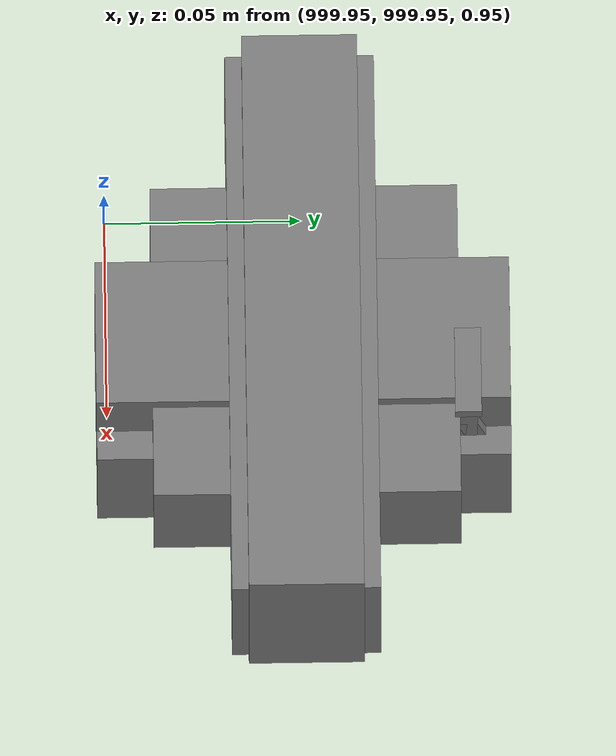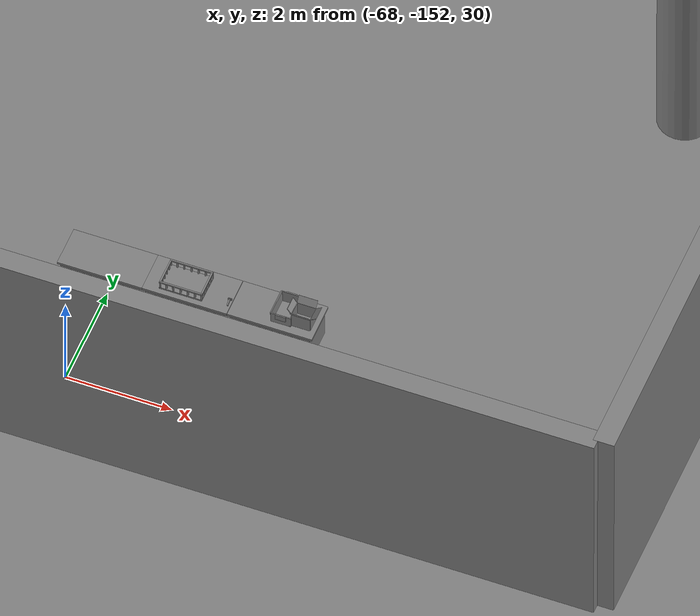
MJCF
<mujoco>
    <option gravity="0.000000000 0.000000000 -9.810000420" timestep="0.0049999999" integrator="implicitfast" density="1.225" viscosity="1.8000001e-05" noslip_iterations="10" iterations="100" sdf_iterations="50">
        <flag multiccd="disable"/>
    </option>
    <size memory="1000M"/>
    <compiler coordinate="local"/>
    <worldbody>
        <light cutoff="30" pos="0 1 1" dir="0 -1 -2"/>
        <light cutoff="30" pos="0 -1 1" dir="0 1 -2"/>
        <body pos="-64.866622925 -149.383972168 30.183746338" euler="89.999984741 89.999946594 0.000000000" name="openloong_gripper_2f85_fix_base_usda_bluebox_01">
            <geom contype="1" conaffinity="1" density="1000" type="box" material="" rgba="0.500000000 0.500000000 0.500000000 1.000000000" solimp="0.899999976 0.949999988 0.001000000" friction="1.000000000 0.005000000 0.000100000" solref="0.020000000 1.000000000" margin="0" condim="3" group="0" pos="0.276580811 0.187225342 0.000068665" quat="0.707106948 0.000077471 0.707106352 0.000077486" size="0.100000001 0.057999998 0.010000000" name="openloong_gripper_2f85_fix_base_usda_geom_B97C93B3_0E0F_4742_89F2_D17EDA0D3921"/>
            <geom contype="1" conaffinity="1" density="1000" type="box" material="" rgba="0.500000000 0.500000000 0.500000000 1.000000000" solimp="0.899999976 0.949999988 0.001000000" friction="1.000000000 0.005000000 0.000100000" solref="0.020000000 1.000000000" margin="0" condim="3" group="0" pos="0.000000000 0.002883911 0.000000000" quat="0.999999881 0.000000000 0.000000000 0.000000000" size="0.254000008 0.003000000 0.172000006" name="openloong_gripper_2f85_fix_base_usda_geom_08FEF5B7_8DC9_4713_9ADE_71BA0D2B7DC4"/>
            <geom contype="1" conaffinity="1" density="1000" type="box" material="" rgba="0.500000000 0.500000000 0.500000000 1.000000000" solimp="0.899999976 0.949999988 0.001000000" friction="1.000000000 0.005000000 0.000100000" solref="0.020000000 1.000000000" margin="0" condim="3" group="0" pos="0.000000000 0.124874115 0.173484802" quat="0.999796331 0.020176515 -0.000000015 0.000000030" size="0.259999990 0.119999997 0.007000000" name="openloong_gripper_2f85_fix_base_usda_geom_76C409A6_5DC0_48D0_B77B_D9BB11571582"/>
            <geom contype="1" conaffinity="1" density="1000" type="box" material="" rgba="0.500000000 0.500000000 0.500000000 1.000000000" solimp="0.899999976 0.949999988 0.001000000" friction="1.000000000 0.005000000 0.000100000" solref="0.020000000 1.000000000" margin="0" condim="3" group="0" pos="0.000000000 0.124874115 -0.173469543" quat="0.999796331 -0.020176545 -0.000000015 0.000000000" size="0.259999990 0.119999997 0.007000000" name="openloong_gripper_2f85_fix_base_usda_geom_BE65082D_A939_49B1_B6FF_F2B32B3152C4"/>
            <geom contype="1" conaffinity="1" density="1000" type="box" material="" rgba="0.500000000 0.500000000 0.500000000 1.000000000" solimp="0.899999976 0.949999988 0.001000000" friction="1.000000000 0.005000000 0.000100000" solref="0.020000000 1.000000000" margin="0" condim="3" group="0" pos="0.000000000 0.214008331 0.188980103" quat="0.999912977 0.013176724 0.000000015 0.000000000" size="0.259999990 0.029999999 0.012500000" name="openloong_gripper_2f85_fix_base_usda_geom_C84D1F37_C250_4F0D_8D19_9E575799D7DA"/>
            <geom contype="1" conaffinity="1" density="1000" type="box" material="" rgba="0.500000000 0.500000000 0.500000000 1.000000000" solimp="0.899999976 0.949999988 0.001000000" friction="1.000000000 0.005000000 0.000100000" solref="0.020000000 1.000000000" margin="0" condim="3" group="0" pos="-0.258361816 0.125289917 0.001876831" quat="0.702796936 -0.020792112 0.710783124 0.020769298" size="0.189999998 0.119999997 0.009000000" name="openloong_gripper_2f85_fix_base_usda_geom_7767892D_7C34_4E9E_A49D_A34B6770BD61"/>
            <geom contype="1" conaffinity="1" density="1000" type="box" material="" rgba="0.500000000 0.500000000 0.500000000 1.000000000" solimp="0.899999976 0.949999988 0.001000000" friction="1.000000000 0.005000000 0.000100000" solref="0.020000000 1.000000000" margin="0" condim="3" group="0" pos="0.000000000 0.214008331 -0.188980103" quat="0.999912977 -0.013176769 0.000000030 0.000000015" size="0.259999990 0.029999999 0.012500000" name="openloong_gripper_2f85_fix_base_usda_geom_722C2580_9BF8_47C3_85E8_508C20A1E495"/>
            <geom contype="1" conaffinity="1" density="1000" type="box" material="" rgba="0.500000000 0.500000000 0.500000000 1.000000000" solimp="0.899999976 0.949999988 0.001000000" friction="1.000000000 0.005000000 0.000100000" solref="0.020000000 1.000000000" margin="0" condim="3" group="0" pos="-0.276611328 0.187225342 0.000068665" quat="0.707106650 0.000077441 0.707106709 0.000077456" size="0.100000001 0.057999998 0.010000000" name="openloong_gripper_2f85_fix_base_usda_geom_E0B602CD_5840_4EAD_B8AC_91B9DC0B030F"/>
            <geom contype="1" conaffinity="1" density="1000" type="box" material="" rgba="0.500000000 0.500000000 0.500000000 1.000000000" solimp="0.899999976 0.949999988 0.001000000" friction="1.000000000 0.005000000 0.000100000" solref="0.020000000 1.000000000" margin="0" condim="3" group="0" pos="0.258331299 0.125289917 0.001876831" quat="0.702851415 0.018856421 0.710823774 -0.019329369" size="0.189999998 0.119999997 0.009000000" name="openloong_gripper_2f85_fix_base_usda_geom_CBB67A28_3B40_469F_9C96_1B7707DF9958"/>
            <freejoint name="openloong_gripper_2f85_fix_base_usda_bluebox_01_joint"/>
            <site size="0.005000000 0.005000000 0.005000000" rgba="0.500000000 0.500000000 0.500000000 1.000000000" pos="0.000000000 0.000000000 0.000000000" quat="0.999961913 0.008726534 0.000000000 0.000000000" group="0" type="sphere" name="openloong_gripper_2f85_fix_base_usda_bluebox_01site"/>
        </body>
        <body pos="-64.496299744 -149.491867065 30.235729218" euler="0.000000000 0.000000000 89.999946594" name="openloong_gripper_2f85_fix_base_usda_cardboardbox_01">
            <geom contype="1" conaffinity="1" density="1000" type="box" material="" rgba="0.500000000 0.500000000 0.500000000 1.000000000" solimp="0.899999976 0.949999988 0.001000000" friction="1.000000000 0.005000000 0.000100000" solref="0.020000000 1.000000000" margin="0" condim="3" group="0" pos="-0.003166199 -0.004086494 0.005052090" quat="1.000000000 0.000000000 0.000000000 0.000000000" size="0.142499998 0.177500010 0.005000000" name="openloong_gripper_2f85_fix_base_usda_geom_4D0EFD35_5DCF_4350_80AE_019AB72E2A0E"/>
            <geom contype="1" conaffinity="1" density="1000" type="box" material="" rgba="0.500000000 0.500000000 0.500000000 1.000000000" solimp="0.899999976 0.949999988 0.001000000" friction="1.000000000 0.005000000 0.000100000" solref="0.020000000 1.000000000" margin="0" condim="3" group="0" pos="-0.003166199 0.170316696 0.150570869" quat="1.000000000 0.000000000 0.000000000 0.000000000" size="0.142499998 0.005000000 0.149999991" name="openloong_gripper_2f85_fix_base_usda_geom_EFD22723_F572_4CFA_ACCC_CA0D1810865A"/>
            <geom contype="1" conaffinity="1" density="1000" type="box" material="" rgba="0.500000000 0.500000000 0.500000000 1.000000000" solimp="0.899999976 0.949999988 0.001000000" friction="1.000000000 0.005000000 0.000100000" solref="0.020000000 1.000000000" margin="0" condim="3" group="0" pos="-0.147399902 -0.005307198 0.150570869" quat="1.000000000 0.000000000 0.000000000 0.000000000" size="0.005000000 0.177500010 0.149999991" name="openloong_gripper_2f85_fix_base_usda_geom_0CE46394_5517_410C_8B28_227C0547C31B"/>
            <geom contype="1" conaffinity="1" density="1000" type="box" material="" rgba="0.500000000 0.500000000 0.500000000 1.000000000" solimp="0.899999976 0.949999988 0.001000000" friction="1.000000000 0.005000000 0.000100000" solref="0.020000000 1.000000000" margin="0" condim="3" group="0" pos="0.140275955 -0.005307198 0.150570869" quat="1.000000000 0.000000000 0.000000000 0.000000000" size="0.005000000 0.177500010 0.149999991" name="openloong_gripper_2f85_fix_base_usda_geom_91ED8D74_26B9_42B5_9E36_F54867CF3E3E"/>
            <geom contype="1" conaffinity="1" density="1000" type="box" material="" rgba="0.500000000 0.500000000 0.500000000 1.000000000" solimp="0.899999976 0.949999988 0.001000000" friction="1.000000000 0.005000000 0.000100000" solref="0.020000000 1.000000000" margin="0" condim="3" group="0" pos="-0.003166199 -0.181550980 0.150570869" quat="1.000000000 0.000000000 0.000000000 0.000000000" size="0.142499998 0.005000000 0.149999991" name="openloong_gripper_2f85_fix_base_usda_geom_005EE62D_040F_4511_B9CB_3E68332E91F3"/>
            <freejoint name="openloong_gripper_2f85_fix_base_usda_cardboardbox_01_joint"/>
            <site size="0.005000000 0.005000000 0.005000000" rgba="0.500000000 0.500000000 0.500000000 1.000000000" pos="0.000000000 0.000000000 0.000000000" quat="0.999961913 0.008726535 0.000000000 0.000000000" group="0" type="sphere" name="openloong_gripper_2f85_fix_base_usda_site_13CBA70A_9477_406F_BD2E_1A4C2BA0DBAE"/>
            <body pos="0.139160156 -0.004048347 0.301930904" euler="-179.999954224 49.383502960 179.999954224" name="openloong_gripper_2f85_fix_base_usda_A1_006">
                <geom contype="1" conaffinity="1" density="1000" type="box" material="" rgba="0.500000000 0.500000000 0.500000000 1.000000000" solimp="0.899999976 0.949999988 0.001000000" friction="1.000000000 0.005000000 0.000100000" solref="0.020000000 1.000000000" margin="0" condim="3" group="0" pos="-0.071587563 0.000009537 0.001745224" quat="0.999999881 0.000000000 0.000000000 0.000000000" size="0.071249999 0.179999992 0.002500000" name="openloong_gripper_2f85_fix_base_usda_geom_E1CDB1C5_5CCE_4E00_8EBC_8797EFA69238"/>
                <joint armature="0" stiffness="0.07" damping="0.0099999998" axis="0.000000 1.000000 0.000000" type="hinge" name="openloong_gripper_2f85_fix_base_usda_A1_006"/>
            </body>
            <body pos="-0.145902634 -0.004086494 0.301938057" euler="-180.000000000 -60.000011444 -180.000000000" name="openloong_gripper_2f85_fix_base_usda_A2_006">
                <geom contype="1" conaffinity="1" density="1000" type="box" material="" rgba="0.500000000 0.500000000 0.500000000 1.000000000" solimp="0.899999976 0.949999988 0.001000000" friction="1.000000000 0.005000000 0.000100000" solref="0.020000000 1.000000000" margin="0" condim="3" group="0" pos="0.071268082 0.000009537 0.002717972" quat="0.000002921 0.000000000 -0.000000030 0.999999881" size="0.071249999 0.179999992 0.002500000" name="openloong_gripper_2f85_fix_base_usda_geom_E4D62CA6_7C76_480D_B191_3496A6EF0656"/>
                <joint armature="0" stiffness="0.07" damping="0.0099999998" axis="0.000000 1.000000 0.000000" type="hinge" name="openloong_gripper_2f85_fix_base_usda_A2_006"/>
            </body>
            <body pos="-0.003385544 0.175991058 0.301930904" euler="-125.858116150 -0.000004561 0.000002331" name="openloong_gripper_2f85_fix_base_usda_B2_006">
                <geom contype="1" conaffinity="1" density="1000" type="box" material="" rgba="0.500000000 0.500000000 0.500000000 1.000000000" solimp="0.899999976 0.949999988 0.001000000" friction="1.000000000 0.005000000 0.000100000" solref="0.020000000 1.000000000" margin="0" condim="3" group="0" pos="0.000009537 -0.070939064 -0.002470016" quat="0.999614120 0.027776197 -0.000000015 0.000000030" size="0.137500003 0.064999998 0.005000000" name="openloong_gripper_2f85_fix_base_usda_geom_3B6372E9_DEE5_4245_B99A_799AEBF761CF"/>
                <joint armature="0" stiffness="0.07" damping="0.0099999998" axis="1.000000 0.000000 0.000000" type="hinge" name="openloong_gripper_2f85_fix_base_usda_B2_006"/>
            </body>
            <body pos="-0.003385544 -0.184140205 0.301938057" euler="147.805557251 0.000000000 0.000000000" name="openloong_gripper_2f85_fix_base_usda_B1_006">
                <geom contype="1" conaffinity="1" density="1000" type="box" material="" rgba="0.500000000 0.500000000 0.500000000 1.000000000" solimp="0.899999976 0.949999988 0.001000000" friction="1.000000000 0.005000000 0.000100000" solref="0.020000000 1.000000000" margin="0" condim="3" group="0" pos="-0.000028610 0.070202351 -0.002703667" quat="0.999614179 -0.027776167 0.000000000 0.000000000" size="0.137500003 0.064999998 0.005000000" name="openloong_gripper_2f85_fix_base_usda_geom_2758AE20_1256_44DF_B08B_105EB3A24624"/>
                <joint armature="0" stiffness="0.07" damping="0.0099999998" axis="1.000000 0.000000 0.000000" type="hinge" name="openloong_gripper_2f85_fix_base_usda_B1_006"/>
            </body>
        </body>
        <body pos="-65.882858276 -149.481979370 30.229999542" euler="-64.487716675 0.000000000 0.000000000" name="openloong_gripper_2f85_fix_base_usda_Barcode">
            <geom contype="1" conaffinity="1" density="1000" type="box" material="" rgba="0.500000000 0.500000000 0.500000000 1.000000000" solimp="0.899999976 0.949999988 0.001000000" friction="1.000000000 0.005000000 0.000100000" solref="0.020000000 1.000000000" margin="0" condim="3" group="0" pos="0.000000000 0.013038635 0.001419067" quat="0.000000000 0.000000000 0.000000000 1.000000119" size="0.034000002 0.010000000 0.017999999" name="openloong_gripper_2f85_fix_base_usda_geom_F6C2BFF0_7436_46D2_85A8_0FAB3BA6D0A4"/>
            <geom contype="1" conaffinity="1" density="1000" type="box" material="" rgba="0.500000000 0.500000000 0.500000000 1.000000000" solimp="0.899999976 0.949999988 0.001000000" friction="1.000000000 0.005000000 0.000100000" solref="0.020000000 1.000000000" margin="0" condim="3" group="0" pos="0.000000000 -0.035301208 -0.007095337" quat="0.000000000 0.000000000 -0.043619365 0.999048233" size="0.028999999 0.010000000 0.020000000" name="openloong_gripper_2f85_fix_base_usda_geom_E6A493FD_CAD8_42F6_8813_1B12A2F1BB2F"/>
            <geom contype="1" conaffinity="1" density="1000" type="box" material="" rgba="0.500000000 0.500000000 0.500000000 1.000000000" solimp="0.899999976 0.949999988 0.001000000" friction="1.000000000 0.005000000 0.000100000" solref="0.020000000 1.000000000" margin="0" condim="3" group="0" pos="0.000000000 -0.043411255 -0.011749268" quat="0.922262907 0.386563420 0.000000000 0.000000000" size="0.026000001 0.010000000 0.020000000" name="openloong_gripper_2f85_fix_base_usda_geom_872851B2_AE9C_44D2_8988_D756ECA89D4B"/>
            <geom contype="1" conaffinity="1" density="1000" type="box" material="" rgba="0.500000000 0.500000000 0.500000000 1.000000000" solimp="0.899999976 0.949999988 0.001000000" friction="1.000000000 0.005000000 0.000100000" solref="0.020000000 1.000000000" margin="0" condim="3" group="0" pos="0.000000000 -0.016967773 -0.031860352" quat="0.000000000 0.000000000 0.000000000 1.000000119" size="0.008000000 0.010000000 0.013000000" name="openloong_gripper_2f85_fix_base_usda_geom_2E3E57DE_6E82_4479_BC56_5677BF4D3701"/>
            <geom contype="1" conaffinity="1" density="1000" type="box" material="" rgba="0.500000000 0.500000000 0.500000000 1.000000000" solimp="0.899999976 0.949999988 0.001000000" friction="1.000000000 0.005000000 0.000100000" solref="0.020000000 1.000000000" margin="0" condim="3" group="0" pos="0.000000000 -0.001869202 0.000312805" quat="0.953716993 0.300705761 0.000000000 0.000000000" size="0.032000002 0.010000000 0.018999999" name="openloong_gripper_2f85_fix_base_usda_geom_94C4C74D_0C08_4498_81BB_0FB85533C850"/>
            <geom contype="1" conaffinity="1" density="1000" type="box" material="" rgba="0.500000000 0.500000000 0.500000000 1.000000000" solimp="0.899999976 0.949999988 0.001000000" friction="1.000000000 0.005000000 0.000100000" solref="0.020000000 1.000000000" margin="0" condim="3" group="0" pos="0.000000000 -0.019531250 -0.003173828" quat="0.953716993 0.300705761 0.000000000 0.000000000" size="0.030999999 0.010000000 0.020000000" name="openloong_gripper_2f85_fix_base_usda_geom_4446993A_7021_437C_867A_BBD715DA7132"/>
            <geom contype="1" conaffinity="1" density="1000" type="box" material="" rgba="0.500000000 0.500000000 0.500000000 1.000000000" solimp="0.899999976 0.949999988 0.001000000" friction="1.000000000 0.005000000 0.000100000" solref="0.020000000 1.000000000" margin="0" condim="3" group="0" pos="0.000000000 -0.035301208 -0.007095337" quat="0.953716993 0.300705761 0.000000000 0.000000000" size="0.028999999 0.010000000 0.020000000" name="openloong_gripper_2f85_fix_base_usda_geom_0397D870_C8E3_460A_B746_79CF880B31BE"/>
            <geom contype="1" conaffinity="1" density="1000" type="box" material="" rgba="0.500000000 0.500000000 0.500000000 1.000000000" solimp="0.899999976 0.949999988 0.001000000" friction="1.000000000 0.005000000 0.000100000" solref="0.020000000 1.000000000" margin="0" condim="3" group="0" pos="0.000000000 -0.042617798 -0.071121216" quat="0.000000000 0.000000000 0.000000000 1.000000119" size="0.013000000 0.021000000 0.059999999" name="openloong_gripper_2f85_fix_base_usda_geom_BE2E2865_00AD_47B1_959B_113C73E85B1D"/>
            <freejoint name="openloong_gripper_2f85_fix_base_usda_Barcode_joint"/>
            <site size="0.005000000 0.005000000 0.005000000" rgba="0.500000000 0.500000000 0.500000000 1.000000000" pos="0.000000000 0.000000000 0.000000000" quat="1.000000000 0.000000000 0.000000000 0.000000000" group="0" type="sphere" name="openloong_gripper_2f85_fix_base_usda_Barcode_site"/>
        </body>
        <body pos="-66.745018005 -149.392349243 30.184000015" euler="0.000000000 0.000000000 89.999946594" name="[22331269298982]_Basket_01">
            <geom contype="1" conaffinity="1" density="1000" type="box" material="" rgba="0.500000000 0.500000000 0.500000000 1.000000000" solimp="0.899999976 0.949999988 0.001000000" friction="1.000000000 0.005000000 0.000100000" solref="0.020000000 1.000000000" margin="0" condim="3" group="0" pos="-0.052425385 0.389207840 0.089787483" quat="0.707107008 0.000000000 0.000000000 0.707106411" size="0.014249999 0.014249999 0.059999999" name="[22331269298982]_geom_8904459C_A4D7_4CF7_84D4_7F4BB6A32F2D"/>
            <geom contype="1" conaffinity="1" density="1000" type="box" material="" rgba="0.500000000 0.500000000 0.500000000 1.000000000" solimp="0.899999976 0.949999988 0.001000000" friction="1.000000000 0.005000000 0.000100000" solref="0.020000000 1.000000000" margin="0" condim="3" group="0" pos="0.264015198 -0.133043289 0.089787483" quat="0.707107008 0.000000000 0.000000000 0.707106411" size="0.014249999 0.014249999 0.059999999" name="[22331269298982]_geom_B93F5C16_7CC6_4390_8448_014217305517"/>
            <geom contype="1" conaffinity="1" density="1000" type="box" material="" rgba="0.500000000 0.500000000 0.500000000 1.000000000" solimp="0.899999976 0.949999988 0.001000000" friction="1.000000000 0.005000000 0.000100000" solref="0.020000000 1.000000000" margin="0" condim="3" group="0" pos="-0.264015198 -0.265548706 0.089793205" quat="0.707107008 0.000000000 0.000000000 0.707106411" size="0.014249999 0.014249999 0.059999999" name="[22331269298982]_geom_66AF7B30_0B55_499B_ABB7_6154608689DE"/>
            <geom contype="1" conaffinity="1" density="1000" type="box" material="" rgba="0.500000000 0.500000000 0.500000000 1.000000000" solimp="0.899999976 0.949999988 0.001000000" friction="1.000000000 0.005000000 0.000100000" solref="0.020000000 1.000000000" margin="0" condim="3" group="0" pos="-0.160263062 -0.389322281 0.089793205" quat="0.707107008 0.000000000 0.000000000 0.707106411" size="0.014249999 0.014249999 0.059999999" name="[22331269298982]_geom_95EFB36D_E918_42EB_A82A_747B66AB8316"/>
            <geom contype="1" conaffinity="1" density="1000" type="box" material="" rgba="0.500000000 0.500000000 0.500000000 1.000000000" solimp="0.899999976 0.949999988 0.001000000" friction="1.000000000 0.005000000 0.000100000" solref="0.020000000 1.000000000" margin="0" condim="3" group="0" pos="0.162265778 -0.389322281 0.089787483" quat="0.707107008 0.000000000 0.000000000 0.707106411" size="0.014249999 0.014249999 0.059999999" name="[22331269298982]_geom_5D20EE5E_B8B7_40AB_8193_480CD9766AB8"/>
            <geom contype="1" conaffinity="1" density="1000" type="box" material="" rgba="0.500000000 0.500000000 0.500000000 1.000000000" solimp="0.899999976 0.949999988 0.001000000" friction="1.000000000 0.005000000 0.000100000" solref="0.020000000 1.000000000" margin="0" condim="3" group="0" pos="0.264015198 0.389207840 0.089787483" quat="0.707107008 0.000000000 0.000000000 0.707106411" size="0.014249999 0.014249999 0.059999999" name="[22331269298982]_geom_6AC49EAE_C419_43A9_B087_FA69BD851C67"/>
            <geom contype="1" conaffinity="1" density="1000" type="box" material="" rgba="0.500000000 0.500000000 0.500000000 1.000000000" solimp="0.899999976 0.949999988 0.001000000" friction="1.000000000 0.005000000 0.000100000" solref="0.020000000 1.000000000" margin="0" condim="3" group="0" pos="-0.264015198 -0.133043289 0.089793205" quat="0.707107008 0.000000000 0.000000000 0.707106411" size="0.014249999 0.014249999 0.059999999" name="[22331269298982]_geom_70559FC7_E8E7_45A8_836B_B9FA0028221B"/>
            <geom contype="1" conaffinity="1" density="1000" type="box" material="" rgba="0.500000000 0.500000000 0.500000000 1.000000000" solimp="0.899999976 0.949999988 0.001000000" friction="1.000000000 0.005000000 0.000100000" solref="0.020000000 1.000000000" margin="0" condim="3" group="0" pos="-0.264026642 0.269256592 0.089793205" quat="0.707107008 0.000000000 0.000000000 0.707106411" size="0.014249999 0.014249999 0.059999999" name="[22331269298982]_geom_EFE319B1_6840_410E_9139_F3102FA49229"/>
            <geom contype="1" conaffinity="1" density="1000" type="box" material="" rgba="0.500000000 0.500000000 0.500000000 1.000000000" solimp="0.899999976 0.949999988 0.001000000" friction="1.000000000 0.005000000 0.000100000" solref="0.020000000 1.000000000" margin="0" condim="3" group="0" pos="0.054462433 0.389207840 0.089787483" quat="0.707107008 0.000000000 0.000000000 0.707106411" size="0.014249999 0.014249999 0.059999999" name="[22331269298982]_geom_EA4637AA_0354_43F7_ADA1_BCF795F7A66B"/>
            <geom contype="1" conaffinity="1" density="1000" type="box" material="" rgba="0.500000000 0.500000000 0.500000000 1.000000000" solimp="0.899999976 0.949999988 0.001000000" friction="1.000000000 0.005000000 0.000100000" solref="0.020000000 1.000000000" margin="0" condim="3" group="0" pos="0.054462433 -0.389322281 0.089787483" quat="0.707107008 0.000000000 0.000000000 0.707106411" size="0.014249999 0.014249999 0.059999999" name="[22331269298982]_geom_0AE17CB6_DAB9_4ECB_8FE1_9963AEE03BDC"/>
            <geom contype="1" conaffinity="1" density="1000" type="box" material="" rgba="0.500000000 0.500000000 0.500000000 1.000000000" solimp="0.899999976 0.949999988 0.001000000" friction="1.000000000 0.005000000 0.000100000" solref="0.020000000 1.000000000" margin="0" condim="3" group="0" pos="0.264015198 0.269256592 0.089793205" quat="0.707107008 0.000000000 0.000000000 0.707106411" size="0.014249999 0.014249999 0.059999999" name="[22331269298982]_geom_6CA287CA_FD3E_4C6E_A194_1DC36C1B70E6"/>
            <geom contype="1" conaffinity="1" density="1000" type="box" material="" rgba="0.500000000 0.500000000 0.500000000 1.000000000" solimp="0.899999976 0.949999988 0.001000000" friction="1.000000000 0.005000000 0.000100000" solref="0.020000000 1.000000000" margin="0" condim="3" group="0" pos="0.264015198 -0.389322281 0.089787483" quat="0.707107008 0.000000000 0.000000000 0.707106411" size="0.014249999 0.014249999 0.059999999" name="[22331269298982]_geom_84DFAF88_75B9_4D90_9D86_A1B34EED7307"/>
            <geom contype="1" conaffinity="1" density="1000" type="box" material="" rgba="0.500000000 0.500000000 0.500000000 1.000000000" solimp="0.899999976 0.949999988 0.001000000" friction="1.000000000 0.005000000 0.000100000" solref="0.020000000 1.000000000" margin="0" condim="3" group="0" pos="0.000000000 0.000000000 0.015998840" quat="0.707107008 0.000000000 0.000000000 0.707106411" size="0.403499991 0.279000014 0.015750000" name="[22331269298982]_geom_ACD2AD5C_1642_4A84_9013_3F066D7D838D"/>
            <geom contype="1" conaffinity="1" density="1000" type="box" material="" rgba="0.500000000 0.500000000 0.500000000 1.000000000" solimp="0.899999976 0.949999988 0.001000000" friction="1.000000000 0.005000000 0.000100000" solref="0.020000000 1.000000000" margin="0" condim="3" group="0" pos="0.000000000 -0.389476776 0.163619041" quat="0.707107008 0.000000000 0.000000000 0.707106411" size="0.015000000 0.277500004 0.015750000" name="[22331269298982]_geom_3E2167D2_6BAB_483D_9313_DFB6B02B197A"/>
            <geom contype="1" conaffinity="1" density="1000" type="box" material="" rgba="0.500000000 0.500000000 0.500000000 1.000000000" solimp="0.899999976 0.949999988 0.001000000" friction="1.000000000 0.005000000 0.000100000" solref="0.020000000 1.000000000" margin="0" condim="3" group="0" pos="0.162265778 0.389207840 0.089787483" quat="0.707107008 0.000000000 0.000000000 0.707106411" size="0.014249999 0.014249999 0.059999999" name="[22331269298982]_geom_60DFB993_880A_4386_AB9C_6BB96CDE5EA0"/>
            <geom contype="1" conaffinity="1" density="1000" type="box" material="" rgba="0.500000000 0.500000000 0.500000000 1.000000000" solimp="0.899999976 0.949999988 0.001000000" friction="1.000000000 0.005000000 0.000100000" solref="0.020000000 1.000000000" margin="0" condim="3" group="0" pos="0.000000000 0.389471054 0.163619041" quat="0.707107008 0.000000000 0.000000000 0.707106411" size="0.015000000 0.277500004 0.015750000" name="[22331269298982]_geom_DB5D52C6_FA2A_4C22_94EC_2508DFEC78A3"/>
            <geom contype="1" conaffinity="1" density="1000" type="box" material="" rgba="0.500000000 0.500000000 0.500000000 1.000000000" solimp="0.899999976 0.949999988 0.001000000" friction="1.000000000 0.005000000 0.000100000" solref="0.020000000 1.000000000" margin="0" condim="3" group="0" pos="-0.263511658 0.000000000 0.163619041" quat="0.707107008 0.000000000 0.000000000 0.707106411" size="0.403499991 0.015000000 0.015750000" name="[22331269298982]_geom_D5A7D600_E402_4DC8_9867_1663CAA9D318"/>
            <geom contype="1" conaffinity="1" density="1000" type="box" material="" rgba="0.500000000 0.500000000 0.500000000 1.000000000" solimp="0.899999976 0.949999988 0.001000000" friction="1.000000000 0.005000000 0.000100000" solref="0.020000000 1.000000000" margin="0" condim="3" group="0" pos="-0.264015198 0.141334534 0.089793205" quat="0.707107008 0.000000000 0.000000000 0.707106411" size="0.014249999 0.014249999 0.059999999" name="[22331269298982]_geom_666A9F6E_C2F2_4C5A_BE08_DC2C08457243"/>
            <geom contype="1" conaffinity="1" density="1000" type="box" material="" rgba="0.500000000 0.500000000 0.500000000 1.000000000" solimp="0.899999976 0.949999988 0.001000000" friction="1.000000000 0.005000000 0.000100000" solref="0.020000000 1.000000000" margin="0" condim="3" group="0" pos="0.264015198 -0.265548706 0.089787483" quat="0.707107008 0.000000000 0.000000000 0.707106411" size="0.014249999 0.014249999 0.059999999" name="[22331269298982]_geom_8ECAF6F0_CFA0_4B71_AAB6_83EFB138536B"/>
            <geom contype="1" conaffinity="1" density="1000" type="box" material="" rgba="0.500000000 0.500000000 0.500000000 1.000000000" solimp="0.899999976 0.949999988 0.001000000" friction="1.000000000 0.005000000 0.000100000" solref="0.020000000 1.000000000" margin="0" condim="3" group="0" pos="-0.160263062 0.389207840 0.089787483" quat="0.707107008 0.000000000 0.000000000 0.707106411" size="0.014249999 0.014249999 0.059999999" name="[22331269298982]_geom_1F8BFCD7_80C9_43F8_9854_B5C208DC5FE0"/>
            <geom contype="1" conaffinity="1" density="1000" type="box" material="" rgba="0.500000000 0.500000000 0.500000000 1.000000000" solimp="0.899999976 0.949999988 0.001000000" friction="1.000000000 0.005000000 0.000100000" solref="0.020000000 1.000000000" margin="0" condim="3" group="0" pos="-0.052425385 -0.389322281 0.089787483" quat="0.707107008 0.000000000 0.000000000 0.707106411" size="0.014249999 0.014249999 0.059999999" name="[22331269298982]_geom_C389B1C2_DE41_4867_A496_D90E06980F80"/>
            <geom contype="1" conaffinity="1" density="1000" type="box" material="" rgba="0.500000000 0.500000000 0.500000000 1.000000000" solimp="0.899999976 0.949999988 0.001000000" friction="1.000000000 0.005000000 0.000100000" solref="0.020000000 1.000000000" margin="0" condim="3" group="0" pos="-0.264026642 -0.389322281 0.089793205" quat="0.707107008 0.000000000 0.000000000 0.707106411" size="0.014249999 0.014249999 0.059999999" name="[22331269298982]_geom_42B89954_0D4B_472B_9123_E8E6C4B44248"/>
            <geom contype="1" conaffinity="1" density="1000" type="box" material="" rgba="0.500000000 0.500000000 0.500000000 1.000000000" solimp="0.899999976 0.949999988 0.001000000" friction="1.000000000 0.005000000 0.000100000" solref="0.020000000 1.000000000" margin="0" condim="3" group="0" pos="0.264015198 0.141334534 0.089787483" quat="0.707107008 0.000000000 0.000000000 0.707106411" size="0.014249999 0.014249999 0.059999999" name="[22331269298982]_geom_A3778F3E_8ECA_4276_AA9C_FC93112F07F4"/>
            <geom contype="1" conaffinity="1" density="1000" type="box" material="" rgba="0.500000000 0.500000000 0.500000000 1.000000000" solimp="0.899999976 0.949999988 0.001000000" friction="1.000000000 0.005000000 0.000100000" solref="0.020000000 1.000000000" margin="0" condim="3" group="0" pos="-0.264015198 0.389207840 0.089793205" quat="0.707107008 0.000000000 0.000000000 0.707106411" size="0.014249999 0.014249999 0.059999999" name="[22331269298982]_geom_1F3CD676_F6A3_4B11_BE99_13BACB92971A"/>
            <geom contype="1" conaffinity="1" density="1000" type="box" material="" rgba="0.500000000 0.500000000 0.500000000 1.000000000" solimp="0.899999976 0.949999988 0.001000000" friction="1.000000000 0.005000000 0.000100000" solref="0.020000000 1.000000000" margin="0" condim="3" group="0" pos="0.264015198 0.004480362 0.089787483" quat="0.707107008 0.000000000 0.000000000 0.707106411" size="0.014249999 0.014249999 0.059999999" name="[22331269298982]_geom_A78EACF6_8132_4948_B196_5311FD84FE86"/>
            <geom contype="1" conaffinity="1" density="1000" type="box" material="" rgba="0.500000000 0.500000000 0.500000000 1.000000000" solimp="0.899999976 0.949999988 0.001000000" friction="1.000000000 0.005000000 0.000100000" solref="0.020000000 1.000000000" margin="0" condim="3" group="0" pos="0.263694763 -0.000011444 0.163619041" quat="0.707107008 0.000000000 0.000000000 0.707106411" size="0.403499991 0.015000000 0.015750000" name="[22331269298982]_geom_C92F2FA0_9E81_4025_9DA8_CA04C2B18F05"/>
            <geom contype="1" conaffinity="1" density="1000" type="box" material="" rgba="0.500000000 0.500000000 0.500000000 1.000000000" solimp="0.899999976 0.949999988 0.001000000" friction="1.000000000 0.005000000 0.000100000" solref="0.020000000 1.000000000" margin="0" condim="3" group="0" pos="-0.264015198 0.004480362 0.089793205" quat="0.707107008 0.000000000 0.000000000 0.707106411" size="0.014249999 0.014249999 0.059999999" name="[22331269298982]_geom_39B9EB1D_6B4A_4F51_9189_199AF33AFCBA"/>
            <freejoint name="[22331269298982]_joint_1EE4DD1C_1426_4370_B229_C1C8FAE8EFF1"/>
        </body>
        <body pos="0.000000000 0.000000000 0.000000000" euler="0.000000000 0.000000000 0.000000000" name="Static Objects_Static Objects">
            <geom contype="1" conaffinity="1" density="1000" type="box" material="" rgba="0.500000000 0.500000000 0.500000000 1.000000000" solimp="0.899999976 0.949999988 0.001000000" friction="1.000000000 0.005000000 0.000100000" solref="0.020000000 1.000000000" margin="0" condim="3" group="0" pos="-67.544113159 -149.365814209 29.727830887" quat="0.500000417 0.499999970 0.499999553 0.499999970" size="0.381000012 0.319999993 0.041000001" name="Static Objects_geom_BFF05C39_5083_4DC1_A1FB_862357663377"/>
            <geom contype="1" conaffinity="1" density="1000" type="box" material="" rgba="0.500000000 0.500000000 0.500000000 1.000000000" solimp="0.899999976 0.949999988 0.001000000" friction="1.000000000 0.005000000 0.000100000" solref="0.020000000 1.000000000" margin="0" condim="3" group="0" pos="-68.239501953 -149.365814209 30.086868286" quat="0.500000417 0.499999970 0.499999553 0.499999970" size="0.370999992 0.039500002 0.745000005" name="Static Objects_geom_985D07E9_0D00_4485_83B5_9B97C1E816E6"/>
            <geom contype="1" conaffinity="1" density="1000" type="box" material="" rgba="0.500000000 0.500000000 0.500000000 1.000000000" solimp="0.899999976 0.949999988 0.001000000" friction="1.000000000 0.005000000 0.000100000" solref="0.020000000 1.000000000" margin="0" condim="3" group="0" pos="-68.239501953 -149.365814209 30.147235870" quat="0.500000417 0.499999970 0.499999553 0.499999970" size="0.400000006 0.022000000 0.800000012" name="Static Objects_geom_4257F8BC_BCCA_48B3_9D2F_CEC291DD598E"/>
            <geom contype="1" conaffinity="1" density="1000" type="box" material="" rgba="0.500000000 0.500000000 0.500000000 1.000000000" solimp="0.899999976 0.949999988 0.001000000" friction="1.000000000 0.005000000 0.000100000" solref="0.020000000 1.000000000" margin="0" condim="3" group="0" pos="-68.934890747 -149.365814209 29.727830887" quat="0.500000417 0.499999970 0.499999553 0.499999970" size="0.381000012 0.319999993 0.041000001" name="Static Objects_geom_DDA88ED4_8C6D_4FAB_9CFE_E64A37E6E2F4"/>
            <geom contype="1" conaffinity="1" density="1000" type="box" material="" rgba="0.500000000 0.500000000 0.500000000 1.000000000" solimp="0.899999976 0.949999988 0.001000000" friction="1.000000000 0.005000000 0.000100000" solref="0.020000000 1.000000000" margin="0" condim="3" group="0" pos="-68.239501953 -149.365814209 29.561563492" quat="0.500000417 0.499999970 0.499999553 0.499999970" size="0.020000000 0.022000000 0.660000026" name="Static Objects_geom_133FE9CF_7594_4563_8C9C_65D4772C5965"/>
            <geom contype="1" conaffinity="1" density="1000" type="box" material="" rgba="0.500000000 0.500000000 0.500000000 1.000000000" solimp="0.899999976 0.949999988 0.001000000" friction="1.000000000 0.005000000 0.000100000" solref="0.020000000 1.000000000" margin="0" condim="3" group="0" pos="-65.945671082 -149.365814209 29.727830887" quat="0.500000417 0.499999970 0.499999553 0.499999970" size="0.381000012 0.319999993 0.041000001" name="Static Objects_geom_47B18528_249F_402B_8D4D_6F8D56A19CAE"/>
            <geom contype="1" conaffinity="1" density="1000" type="box" material="" rgba="0.500000000 0.500000000 0.500000000 1.000000000" solimp="0.899999976 0.949999988 0.001000000" friction="1.000000000 0.005000000 0.000100000" solref="0.020000000 1.000000000" margin="0" condim="3" group="0" pos="-66.641059875 -149.365814209 30.086868286" quat="0.500000417 0.499999970 0.499999553 0.499999970" size="0.370999992 0.039500002 0.745000005" name="Static Objects_geom_2FF174D0_88C6_48F8_B278_5F16EAEC6860"/>
            <geom contype="1" conaffinity="1" density="1000" type="box" material="" rgba="0.500000000 0.500000000 0.500000000 1.000000000" solimp="0.899999976 0.949999988 0.001000000" friction="1.000000000 0.005000000 0.000100000" solref="0.020000000 1.000000000" margin="0" condim="3" group="0" pos="-66.641059875 -149.365814209 30.147235870" quat="0.500000417 0.499999970 0.499999553 0.499999970" size="0.400000006 0.022000000 0.800000012" name="Static Objects_geom_7DA6A68E_8ED7_409A_8FD3_9DE80D043659"/>
            <geom contype="1" conaffinity="1" density="1000" type="box" material="" rgba="0.500000000 0.500000000 0.500000000 1.000000000" solimp="0.899999976 0.949999988 0.001000000" friction="1.000000000 0.005000000 0.000100000" solref="0.020000000 1.000000000" margin="0" condim="3" group="0" pos="-67.336448669 -149.365814209 29.727830887" quat="0.500000417 0.499999970 0.499999553 0.499999970" size="0.381000012 0.319999993 0.041000001" name="Static Objects_geom_5ADC4AA8_420B_4212_9C15_0DF97640BD33"/>
            <geom contype="1" conaffinity="1" density="1000" type="box" material="" rgba="0.500000000 0.500000000 0.500000000 1.000000000" solimp="0.899999976 0.949999988 0.001000000" friction="1.000000000 0.005000000 0.000100000" solref="0.020000000 1.000000000" margin="0" condim="3" group="0" pos="-66.641059875 -149.365814209 29.561563492" quat="0.500000417 0.499999970 0.499999553 0.499999970" size="0.020000000 0.022000000 0.660000026" name="Static Objects_geom_4A51BD3C_E6CF_4D68_83A0_71CAF176A531"/>
            <geom contype="1" conaffinity="1" density="1000" type="box" material="" rgba="0.500000000 0.500000000 0.500000000 1.000000000" solimp="0.899999976 0.949999988 0.001000000" friction="1.000000000 0.005000000 0.000100000" solref="0.020000000 1.000000000" margin="0" condim="3" group="0" pos="-64.338577271 -149.365814209 29.727830887" quat="0.500000417 0.499999970 0.499999553 0.499999970" size="0.381000012 0.319999993 0.041000001" name="Static Objects_geom_8B483A6E_1604_452A_8FAA_628C2E8579D7"/>
            <geom contype="1" conaffinity="1" density="1000" type="box" material="" rgba="0.500000000 0.500000000 0.500000000 1.000000000" solimp="0.899999976 0.949999988 0.001000000" friction="1.000000000 0.005000000 0.000100000" solref="0.020000000 1.000000000" margin="0" condim="3" group="0" pos="-65.033966064 -149.365814209 30.086868286" quat="0.500000417 0.499999970 0.499999553 0.499999970" size="0.370999992 0.039500002 0.745000005" name="Static Objects_geom_0529859E_064D_487B_BEED_BC2E7A89853A"/>
            <geom contype="1" conaffinity="1" density="1000" type="box" material="" rgba="0.500000000 0.500000000 0.500000000 1.000000000" solimp="0.899999976 0.949999988 0.001000000" friction="1.000000000 0.005000000 0.000100000" solref="0.020000000 1.000000000" margin="0" condim="3" group="0" pos="-65.033966064 -149.365814209 30.147235870" quat="0.500000417 0.499999970 0.499999553 0.499999970" size="0.400000006 0.022000000 0.800000012" name="Static Objects_geom_43E7A129_7DC2_40BB_AAD0_50C90F918D96"/>
            <geom contype="1" conaffinity="1" density="1000" type="box" material="" rgba="0.500000000 0.500000000 0.500000000 1.000000000" solimp="0.899999976 0.949999988 0.001000000" friction="1.000000000 0.005000000 0.000100000" solref="0.020000000 1.000000000" margin="0" condim="3" group="0" pos="-65.729354858 -149.365814209 29.727830887" quat="0.500000417 0.499999970 0.499999553 0.499999970" size="0.381000012 0.319999993 0.041000001" name="Static Objects_geom_5CC44F59_8484_4F4B_B2E0_9C48038FA8C6"/>
            <geom contype="1" conaffinity="1" density="1000" type="box" material="" rgba="0.500000000 0.500000000 0.500000000 1.000000000" solimp="0.899999976 0.949999988 0.001000000" friction="1.000000000 0.005000000 0.000100000" solref="0.020000000 1.000000000" margin="0" condim="3" group="0" pos="-65.033966064 -149.365814209 29.561563492" quat="0.500000417 0.499999970 0.499999553 0.499999970" size="0.020000000 0.022000000 0.660000026" name="Static Objects_geom_CCC967C2_DE66_4D70_9A02_C38A1B28E3A9"/>
            <geom contype="1" conaffinity="1" density="1000" type="box" material="" rgba="0.500000000 0.500000000 0.500000000 1.000000000" solimp="0.899999976 0.949999988 0.001000000" friction="1.000000000 0.005000000 0.000100000" solref="0.020000000 1.000000000" margin="0" condim="3" group="0" pos="-61.754566193 -137.853729248 33.906845093" quat="0.707107067 0.000000000 0.000000000 0.707106471" size="0.759999990 0.759999990 4.500000000" name="Static Objects_geom_28DF04A5_641A_4C99_A5BD_8DF3C9BD2D5F"/>
            <geom contype="1" conaffinity="1" density="1000" type="box" material="" rgba="0.500000000 0.500000000 0.500000000 1.000000000" solimp="0.899999976 0.949999988 0.001000000" friction="1.000000000 0.005000000 0.000100000" solref="0.020000000 1.000000000" margin="0" condim="3" group="0" pos="-57.511135101 -144.927108765 31.707921982" quat="1.000000000 0.000000000 0.000000000 0.000000000" size="0.200000003 8.000000000 2.299999952" name="Static Objects_geom_65349A58_F587_4924_849F_859B93DD222D"/>
            <geom contype="1" conaffinity="1" density="1000" type="box" material="" rgba="0.500000000 0.500000000 0.500000000 1.000000000" solimp="0.899999976 0.949999988 0.001000000" friction="1.000000000 0.005000000 0.000100000" solref="0.020000000 1.000000000" margin="0" condim="3" group="0" pos="-80.517646790 -157.574050903 31.688196182" quat="0.707107067 0.000000000 0.000000000 0.707106471" size="0.600000024 0.600000024 2.299999952" name="Static Objects_geom_33897A9C_F3AB_49C9_B0E0_C6BBA1E675D7"/>
            <geom contype="1" conaffinity="1" density="1000" type="box" material="" rgba="0.500000000 0.500000000 0.500000000 1.000000000" solimp="0.899999976 0.949999988 0.001000000" friction="1.000000000 0.005000000 0.000100000" solref="0.020000000 1.000000000" margin="0" condim="3" group="0" pos="-80.711044312 -147.414932251 31.666158676" quat="1.000000000 0.000000000 0.000000000 0.000000000" size="0.200000003 10.000000000 2.299999952" name="Static Objects_geom_A1D2F94C_B077_41D1_A9EA_6EB2B33CDD70"/>
            <geom contype="1" conaffinity="1" density="1000" type="box" material="" rgba="0.500000000 0.500000000 0.500000000 1.000000000" solimp="0.899999976 0.949999988 0.001000000" friction="1.000000000 0.005000000 0.000100000" solref="0.020000000 1.000000000" margin="0" condim="3" group="0" pos="-57.687217712 -137.434692383 31.688196182" quat="0.707107067 0.000000000 0.000000000 0.707106471" size="0.600000024 0.600000024 2.299999952" name="Static Objects_geom_6065E0CF_98C8_446A_B275_838BEF5B9806"/>
            <geom contype="1" conaffinity="1" density="1000" type="box" material="" rgba="0.500000000 0.500000000 0.500000000 1.000000000" solimp="0.899999976 0.949999988 0.001000000" friction="1.000000000 0.005000000 0.000100000" solref="0.020000000 1.000000000" margin="0" condim="3" group="0" pos="-69.537033081 -140.263229370 31.714921951" quat="0.707107067 0.000000000 0.000000000 0.707106471" size="0.759999990 4.500000000 2.299999952" name="Static Objects_geom_14924B62_9AE7_40E6_BFB0_92B96F8E4F45"/>
            <geom contype="1" conaffinity="1" density="1000" type="box" material="" rgba="0.500000000 0.500000000 0.500000000 1.000000000" solimp="0.899999976 0.949999988 0.001000000" friction="1.000000000 0.005000000 0.000100000" solref="0.020000000 1.000000000" margin="0" condim="3" group="0" pos="-80.073638916 -137.853713989 33.906845093" quat="0.707107067 0.000000000 0.000000000 0.707106471" size="0.759999990 0.759999990 4.500000000" name="Static Objects_geom_1FEB9366_E5E6_4FC3_B74B_F5A185839951"/>
            <geom contype="1" conaffinity="1" density="1000" type="box" material="" rgba="0.500000000 0.500000000 0.500000000 1.000000000" solimp="0.899999976 0.949999988 0.001000000" friction="1.000000000 0.005000000 0.000100000" solref="0.020000000 1.000000000" margin="0" condim="3" group="0" pos="-73.406707764 -155.734664917 31.707921982" quat="1.000000000 0.000000000 0.000000000 0.000000000" size="0.200000003 3.000000000 2.299999952" name="Static Objects_geom_34F14F4C_6FE7_4194_A4C4_9FBC99F90B73"/>
            <geom contype="1" conaffinity="1" density="1000" type="box" material="" rgba="0.500000000 0.500000000 0.500000000 1.000000000" solimp="0.899999976 0.949999988 0.001000000" friction="1.000000000 0.005000000 0.000100000" solref="0.020000000 1.000000000" margin="0" condim="3" group="0" pos="-68.497543335 -137.448257446 31.707921982" quat="0.707107067 0.000000000 0.000000000 0.707106471" size="0.200000003 14.000000000 2.299999952" name="Static Objects_geom_66F58F4E_C10B_4616_AA6F_3162CF1BD9B4"/>
            <geom contype="1" conaffinity="1" density="1000" type="cylinder" material="" rgba="0.500000000 0.500000000 0.500000000 1.000000000" solimp="0.899999976 0.949999988 0.001000000" friction="1.000000000 0.005000000 0.000100000" solref="0.020000000 1.000000000" margin="0" condim="3" group="0" pos="-68.868522644 -142.134506226 31.711090088" quat="0.707107067 0.000000000 0.000000000 0.707106471" size="0.509999990 2.299999952 1.000000000" name="Static Objects_geom_B3DCE6BE_4B1F_4643_AAAE_52DC52ECCF5F"/>
            <geom contype="1" conaffinity="1" density="1000" type="plane" material="" rgba="0.500000000 0.500000000 0.500000000 1.000000000" solimp="0.899999976 0.949999988 0.001000000" friction="1.000000000 0.005000000 0.000100000" solref="0.020000000 1.000000000" margin="0" condim="3" group="0" pos="-72.873703003 -147.131927490 29.409669876" quat="1.000000000 0.000000000 0.000000000 0.000000000" size="18.000000000 14.000000000 1.000000000" name="Static Objects_geom_CFF725A2_F52F_4393_AA1D_E1555220368D"/>
            <geom contype="1" conaffinity="1" density="1000" type="box" material="" rgba="0.500000000 0.500000000 0.500000000 1.000000000" solimp="0.899999976 0.949999988 0.001000000" friction="1.000000000 0.005000000 0.000100000" solref="0.020000000 1.000000000" margin="0" condim="3" group="0" pos="-79.943580627 -157.782272339 31.707921982" quat="0.707107067 0.000000000 0.000000000 0.707106471" size="0.200000003 7.000000000 2.299999952" name="Static Objects_geom_5155730A_606E_44C2_9822_1274F8EEB512"/>
            <geom contype="1" conaffinity="1" density="1000" type="box" material="" rgba="0.500000000 0.500000000 0.500000000 1.000000000" solimp="0.899999976 0.949999988 0.001000000" friction="1.000000000 0.005000000 0.000100000" solref="0.020000000 1.000000000" margin="0" condim="3" group="0" pos="-65.421028137 -152.903442383 31.707921982" quat="0.707107067 0.000000000 0.000000000 0.707106471" size="0.200000003 7.800000191 2.299999952" name="Static Objects_geom_1050C27A_7A99_4A48_9AD7_D3C5CE37135A"/>
            <geom contype="1" conaffinity="1" density="1000" type="box" material="" rgba="0.500000000 0.500000000 0.500000000 1.000000000" solimp="0.899999976 0.949999988 0.001000000" friction="1.000000000 0.005000000 0.000100000" solref="0.020000000 1.000000000" margin="0" condim="3" group="0" pos="-74.776908875 -149.964416504 31.688196182" quat="1.000000000 0.000000000 0.000000000 0.000000000" size="0.600000024 0.409999996 2.299999952" name="Static Objects_geom_A70E902B_BF00_44B9_A2C4_995469AB92BC"/>
            <geom contype="1" conaffinity="1" density="1000" type="cylinder" material="" rgba="0.500000000 0.500000000 0.500000000 1.000000000" solimp="0.899999976 0.949999988 0.001000000" friction="1.000000000 0.005000000 0.000100000" solref="0.020000000 1.000000000" margin="0" condim="3" group="0" pos="-60.161884308 -142.134506226 31.711090088" quat="0.707107067 0.000000000 0.000000000 0.707106471" size="0.509999990 2.299999952 1.000000000" name="Static Objects_geom_1FE807E6_A8DC_4B22_B08D_9F2C11499C27"/>
            <geom contype="1" conaffinity="1" density="1000" type="cylinder" material="" rgba="0.500000000 0.500000000 0.500000000 1.000000000" solimp="0.899999976 0.949999988 0.001000000" friction="1.000000000 0.005000000 0.000100000" solref="0.020000000 1.000000000" margin="0" condim="3" group="0" pos="-75.382453918 -149.963455200 31.711090088" quat="0.707107067 0.000000000 0.000000000 0.707106471" size="0.409999996 2.299999952 1.000000000" name="Static Objects_geom_724EBA1D_6033_47CA_A6FC_B8DB030B094A"/>
            <geom contype="1" conaffinity="1" density="1000" type="cylinder" material="" rgba="0.500000000 0.500000000 0.500000000 1.000000000" solimp="0.899999976 0.949999988 0.001000000" friction="1.000000000 0.005000000 0.000100000" solref="0.020000000 1.000000000" margin="0" condim="3" group="0" pos="-74.154960632 -149.963455200 31.711090088" quat="0.707107067 0.000000000 0.000000000 0.707106471" size="0.409999996 2.299999952 1.000000000" name="Static Objects_geom_60744639_E8E3_4777_AE3F_97D0D62692CE"/>
            <geom contype="1" conaffinity="1" density="1000" type="cylinder" material="" rgba="0.500000000 0.500000000 0.500000000 1.000000000" solimp="0.899999976 0.949999988 0.001000000" friction="1.000000000 0.005000000 0.000100000" solref="0.020000000 1.000000000" margin="0" condim="3" group="0" pos="-77.566612244 -142.134506226 31.711090088" quat="0.707107067 0.000000000 0.000000000 0.707106471" size="0.509999990 2.299999952 1.000000000" name="Static Objects_geom_2AEBC133_2BEF_4E1E_9608_D4BD9B9BB771"/>
        </body>
        <body pos="-65.813888550 -149.620910645 31.165815353" euler="-123.085182190 62.578792572 -94.967849731" mocap="true" name="spotlight6_SpotLight"/>
        <body pos="1000.000000000 1000.000000000 1.000000000" euler="0.000000000 0.000000000 180.000000000" name="openloong_gripper_2f85_fix_base_usda_wifi_box">
            <geom contype="1" conaffinity="1" density="1000" type="box" material="" rgba="0.500000000 0.500000000 0.500000000 1.000000000" solimp="0.899999976 0.949999988 0.001000000" friction="1.000000000 0.005000000 0.000100000" solref="0.020000000 1.000000000" margin="0" condim="3" group="0" pos="0.000000000 0.000000000 0.058978677" quat="0.000000000 0.000000047 0.000000000 1.000000000" size="0.068499997 0.018999999 0.059000000" name="openloong_gripper_2f85_fix_base_usda_geom_A20434F7_E3F9_4CC6_9FB2_FA1FC3C6A03B"/>
            <freejoint name="openloong_gripper_2f85_fix_base_usda_wifi_box_joint"/>
            <site size="0.005000000 0.005000000 0.005000000" rgba="0.500000000 0.500000000 0.500000000 1.000000000" pos="0.000000000 0.000000000 0.000000000" quat="0.999961913 0.008726500 0.000000000 0.000000000" group="0" type="sphere" name="openloong_gripper_2f85_fix_base_usda_wifi_boxsite"/>
        </body>
        <body pos="1000.000000000 1000.000000000 1.000000000" euler="0.000000000 0.000000000 180.000000000" name="openloong_gripper_2f85_fix_base_usda_battery_01">
            <geom contype="1" conaffinity="1" density="1000" type="box" material="" rgba="0.500000000 0.500000000 0.500000000 1.000000000" solimp="0.899999976 0.949999988 0.001000000" friction="1.000000000 0.005000000 0.000100000" solref="0.020000000 1.000000000" margin="0" condim="3" group="0" pos="-0.011123657 -0.041940309 0.101691343" quat="1.000000000 0.000000000 0.000000000 0.000000000" size="0.010800000 0.003375000 0.004725000" name="openloong_gripper_2f85_fix_base_usda_geom_7B5AC288_EEFC_4FB3_A80E_98D483AEBCD6"/>
            <geom contype="1" conaffinity="1" density="1000" type="box" material="" rgba="0.500000000 0.500000000 0.500000000 1.000000000" solimp="0.899999976 0.949999988 0.001000000" friction="1.000000000 0.005000000 0.000100000" solref="0.020000000 1.000000000" margin="0" condim="3" group="0" pos="-0.010876465 -0.044247437 0.047066893" quat="0.998702705 -0.050920475 0.000000000 0.000000000" size="0.009450001 0.002700000 0.024975000" name="openloong_gripper_2f85_fix_base_usda_geom_0D2FFD82_B0E5_49C0_8143_163BFE405F76"/>
            <geom contype="1" conaffinity="1" density="1000" type="box" material="" rgba="0.500000000 0.500000000 0.500000000 1.000000000" solimp="0.899999976 0.949999988 0.001000000" friction="1.000000000 0.005000000 0.000100000" solref="0.020000000 1.000000000" margin="0" condim="3" group="0" pos="-0.001235962 -0.000659180 0.047381196" quat="1.000000000 0.000000000 0.000000000 0.000000000" size="0.039420001 0.039150000 0.047250003" name="openloong_gripper_2f85_fix_base_usda_geom_86C83278_E037_4E1B_B951_F015BD8CBB13"/>
            <geom contype="1" conaffinity="1" density="1000" type="box" material="" rgba="0.500000000 0.500000000 0.500000000 1.000000000" solimp="0.899999976 0.949999988 0.001000000" friction="1.000000000 0.005000000 0.000100000" solref="0.020000000 1.000000000" margin="0" condim="3" group="0" pos="-0.010876465 -0.039138794 0.009851727" quat="1.000000000 0.000000000 0.000000000 0.000000000" size="0.009450001 0.010800000 0.013500000" name="openloong_gripper_2f85_fix_base_usda_geom_D1D5E1A7_D951_4995_BDFE_6E1537323E9F"/>
            <geom contype="1" conaffinity="1" density="1000" type="box" material="" rgba="0.500000000 0.500000000 0.500000000 1.000000000" solimp="0.899999976 0.949999988 0.001000000" friction="1.000000000 0.005000000 0.000100000" solref="0.020000000 1.000000000" margin="0" condim="3" group="0" pos="-0.010876465 -0.041528322 0.071508206" quat="1.000000000 0.000000000 0.000000000 0.000000000" size="0.009450001 0.002700000 0.027000001" name="openloong_gripper_2f85_fix_base_usda_geom_A117E878_3D11_4C43_A9A8_9FC3C1A952DF"/>
            <freejoint name="openloong_gripper_2f85_fix_base_usda_battery_01_joint"/>
            <site size="0.005000000 0.005000000 0.005000000" rgba="0.500000000 0.500000000 0.500000000 1.000000000" pos="0.000000000 0.000000000 0.000000000" quat="0.999961913 0.008726500 0.000000000 0.000000000" group="0" type="sphere" name="openloong_gripper_2f85_fix_base_usda_battery_01site"/>
        </body>
        <body pos="1000.000000000 1000.000000000 1.000000000" euler="0.000000000 0.000000000 180.000000000" name="openloong_gripper_2f85_fix_base_usda_cpu_fan">
            <geom contype="1" conaffinity="1" density="1000" type="box" material="" rgba="0.500000000 0.500000000 0.500000000 1.000000000" solimp="0.899999976 0.949999988 0.001000000" friction="1.000000000 0.005000000 0.000100000" solref="0.020000000 1.000000000" margin="0" condim="3" group="0" pos="0.000000000 0.000000000 0.070034981" quat="0.000000000 0.000000000 0.000000000 1.000000000" size="0.070700005 0.014699999 0.070700005" name="openloong_gripper_2f85_fix_base_usda_geom_323EE24A_0380_4E41_B94D_B53F87DD3F23"/>
            <freejoint name="openloong_gripper_2f85_fix_base_usda_cpu_fan_joint"/>
            <site size="0.005000000 0.005000000 0.005000000" rgba="0.500000000 0.500000000 0.500000000 1.000000000" pos="0.000000000 0.000000000 0.000000000" quat="0.999961913 0.008726535 0.000000000 0.000000000" group="0" type="sphere" name="openloong_gripper_2f85_fix_base_usda_cpu_fancsite"/>
        </body>
        <body pos="1000.000000000 1000.000000000 1.000000000" euler="0.000011953 0.000005123 -179.999984741" name="openloong_gripper_2f85_fix_base_usda_intel_box">
            <geom contype="1" conaffinity="1" density="1000" type="box" material="" rgba="0.500000000 0.500000000 0.500000000 1.000000000" solimp="0.899999976 0.949999988 0.001000000" friction="1.000000000 0.005000000 0.000100000" solref="0.020000000 1.000000000" margin="0" condim="3" group="0" pos="0.000000000 -0.000067139 0.000082284" quat="0.707106709 0.000000225 0.000000253 0.707106650" size="0.052800003 0.025300000 0.052800003" name="openloong_gripper_2f85_fix_base_usda_geom_713A2E34_7747_44E3_ADB5_7ED218B116B1"/>
            <freejoint name="openloong_gripper_2f85_fix_base_usda_intel_box_joint"/>
            <site size="0.005000000 0.005000000 0.005000000" rgba="0.500000000 0.500000000 0.500000000 1.000000000" pos="0.000000000 0.000000000 0.000000000" quat="0.999961913 0.008726500 0.000000000 0.000000000" group="0" type="sphere" name="openloong_gripper_2f85_fix_base_usda_intel_boxsite"/>
        </body>
        <body pos="-65.900627136 -149.052734375 31.171289444" euler="144.638488770 -49.615707397 -130.324218750" mocap="true" name="spotlight5_SpotLight"/>
        <body pos="1000.000000000 999.999938965 1.000000000" euler="0.000000000 0.000000000 180.000000000" name="openloong_gripper_2f85_fix_base_usda_intelcore_i5">
            <geom contype="1" conaffinity="1" density="1000" type="box" material="" rgba="0.500000000 0.500000000 0.500000000 1.000000000" solimp="0.899999976 0.949999988 0.001000000" friction="1.000000000 0.005000000 0.000100000" solref="0.020000000 1.000000000" margin="0" condim="3" group="0" pos="0.000000000 0.000000000 0.051722717" quat="0.707106709 0.000000000 0.000000000 -0.707106769" size="0.052800000 0.018080002 0.052800000" name="openloong_gripper_2f85_fix_base_usda_geom_6B458564_E525_4A1D_8676_E627485580E2"/>
            <freejoint name="openloong_gripper_2f85_fix_base_usda_intelcore_i5_joint"/>
            <site size="0.005000000 0.005000000 0.005000000" rgba="0.500000000 0.500000000 0.500000000 1.000000000" pos="0.000000000 0.000000000 0.000000000" quat="0.999961913 0.008726534 0.000000000 0.000000000" group="0" type="sphere" name="openloong_gripper_2f85_fix_base_usda_intelcore_i5site"/>
        </body>
        <body pos="-66.100212097 -149.317779541 31.164623260" euler="114.984237671 2.629695415 128.302047729" mocap="true" name="spotlight4_SpotLight"/>
        <body pos="-66.291030884 -149.869689941 29.018842697" euler="0.000000000 0.000000000 89.999946594" mocap="true" name="openloong_gripper_2f85_fix_base_usda_leftHandMocap"/>
        <body pos="-66.291030884 -149.869689941 29.018842697" euler="0.000000000 0.000000000 89.999946594" mocap="true" name="openloong_gripper_2f85_fix_base_usda_rightHandMocap"/>
        <body pos="-66.291030884 -149.869689941 30.218843460" euler="0.000000000 0.000000000 89.999946594" name="openloong_gripper_2f85_fix_base_usda_base_link">
            <geom contype="1" conaffinity="1" density="1000" type="mesh" material="" rgba="0.783999979 0.783999979 0.783999979 1.000000000" solimp="0.899999976 0.949999988 0.001000000" friction="1.000000000 0.005000000 0.000100000" solref="0.020000000 1.000000000" margin="0" condim="3" group="3" mesh="base_link" pos="0.000000000 0.000000000 0.000000000" quat="1.000000000 0.000000000 0.000000000 0.000000000" size="1.000000000 1.000000000 1.000000000" name="openloong_gripper_2f85_fix_base_usda__geom_7_7408FB69_E255_495A_98DB_4C2056BF097F"/>
            <site size="0.005000000 0.005000000 0.005000000" rgba="0.500000000 0.500000000 0.500000000 1.000000000" pos="0.000000000 0.000000000 0.000000000" quat="1.000000000 0.000000000 0.000000000 0.000000000" group="0" type="sphere" name="openloong_gripper_2f85_fix_base_usda_imu"/>
            <inertial mass="22.447001" pos="-0.005664100 -0.001336700 0.238289997" diaginertia="0.374352545 0.277180195 0.220617250" quat="0.999247074 0.035235517 -0.015086859 0.006023135"/>
            <body pos="0.000000000 0.000000000 0.299997330" euler="0.000000000 0.000000000 0.000000000" name="openloong_gripper_2f85_fix_base_usda_dummy_body">
                <geom contype="1" conaffinity="1" density="1000" type="sphere" material="" rgba="0.783999979 0.783999979 0.783999979 1.000000000" solimp="0.899999976 0.949999988 0.001000000" friction="1.000000000 0.005000000 0.000100000" solref="0.020000000 1.000000000" margin="0" condim="3" group="3" pos="0.000000000 0.000000000 0.000000000" quat="1.000000000 0.000000000 0.000000000 0.000000000" size="0.010000000 0.000000000 0.000000000" name="openloong_gripper_2f85_fix_base_usda__geom_8_26805DC7_8746_42D2_8A72_E9DF1C5B775F"/>
                <joint armature="0.0099999998" stiffness="0" damping="0.1" axis="0.000000 0.000000 1.000000" type="hinge" name="openloong_gripper_2f85_fix_base_usda_dummy_joint"/>
                <site size="0.010000000 0.005000000 0.005000000" rgba="0.500000000 0.500000000 0.500000000 1.000000000" pos="0.000000000 0.000000000 0.000000000" quat="1.000000000 0.000000000 0.000000000 0.000000000" group="3" type="sphere" name="openloong_gripper_2f85_fix_base_usda_dummy_site"/>
            </body>
            <body pos="0.009002686 0.000000000 0.406400681" euler="0.000000000 0.000000000 0.000000000" name="openloong_gripper_2f85_fix_base_usda_Link_head_yaw">
                <geom contype="1" conaffinity="1" density="1000" type="mesh" material="" rgba="0.783999979 0.783999979 0.783999979 1.000000000" solimp="0.899999976 0.949999988 0.001000000" friction="1.000000000 0.005000000 0.000100000" solref="0.020000000 1.000000000" margin="0" condim="3" group="3" mesh="Link_head_yaw" pos="0.000000000 0.000000000 0.000000000" quat="1.000000000 0.000000000 0.000000000 0.000000000" size="1.000000000 1.000000000 1.000000000" name="openloong_gripper_2f85_fix_base_usda__geom_10_55F55A1B_C1C4_47BA_A538_5C055A895F2A"/>
                <inertial mass="0.84249002" pos="0.000000000 -0.002081400 0.044801001" diaginertia="0.000700588 0.000629000 0.000553812" quat="0.706933022 -0.015675601 0.015677100 0.706933022"/>
                <body pos="0.000000000 -0.034599304 0.048500061" euler="0.000000000 0.000000000 0.000000000" name="openloong_gripper_2f85_fix_base_usda_Link_head_pitch">
                    <geom contype="1" conaffinity="1" density="1000" type="mesh" material="" rgba="0.783999979 0.783999979 0.783999979 1.000000000" solimp="0.899999976 0.949999988 0.001000000" friction="1.000000000 0.005000000 0.000100000" solref="0.020000000 1.000000000" margin="0" condim="3" group="3" mesh="Link_head_pitch" pos="0.000000000 0.000000000 0.000000000" quat="1.000000000 0.000000000 0.000000000 0.000000000" size="1.000000000 1.000000000 1.000000000" name="openloong_gripper_2f85_fix_base_usda__geom_12_ACB812B8_B497_4ECB_AF1E_B88838056B0F"/>
                    <inertial mass="1.3943" pos="0.020569000 0.033004001 0.125000000" diaginertia="0.006381400 0.006289940 0.004481460" quat="0.973390222 0.008406822 0.228157058 0.019624906"/>
                    <body pos="0.000000000 0.029998779 0.000000000" euler="0.000000000 0.000000000 0.000000000" name="openloong_gripper_2f85_fix_base_usda_neck_center_body">
                        <site size="0.010000000 0.005000000 0.005000000" rgba="0.500000000 0.500000000 0.500000000 1.000000000" pos="0.000000000 0.000000000 0.000000000" quat="1.000000000 0.000000000 0.000000000 0.000000000" group="3" type="sphere" name="openloong_gripper_2f85_fix_base_usda_neck_center_site"/>
                        <body pos="0.020004272 0.000000000 0.149999619" euler="-0.000002229 39.998176575 -90.000205994" name="openloong_gripper_2f85_fix_base_usda_camera_head">
                            <site size="0.010000000 0.005000000 0.005000000" rgba="0.500000000 0.500000000 0.500000000 1.000000000" pos="0.000000000 0.000000000 0.000000000" quat="1.000000000 0.000000000 0.000000000 0.000000000" group="3" type="sphere" name="openloong_gripper_2f85_fix_base_usda_camera_head_site"/>
                        </body>
                    </body>
                </body>
            </body>
            <body pos="0.003997803 -0.161598206 0.392200470" euler="0.000000000 0.000000000 0.000000000" name="openloong_gripper_2f85_fix_base_usda_Link_arm_r_01">
                <geom contype="1" conaffinity="1" density="1000" type="mesh" material="" rgba="0.783999979 0.783999979 0.783999979 1.000000000" solimp="0.899999976 0.949999988 0.001000000" friction="1.000000000 0.005000000 0.000100000" solref="0.020000000 1.000000000" margin="0" condim="3" group="3" mesh="Link_arm_r_01" pos="0.000000000 0.000000000 0.000000000" quat="1.000000000 0.000000000 0.000000000 0.000000000" size="1.000000000 1.000000000 1.000000000" name="openloong_gripper_2f85_fix_base_usda__geom_14_024D8808_FC7B_40B0_88DB_8DA94EC01C6E"/>
                <joint armature="0.0099999998" stiffness="0" damping="1" axis="0.000000 -1.000000 0.000000" limited="true" range="-170.000015259 170.000015259" type="hinge" name="openloong_gripper_2f85_fix_base_usda_J_arm_r_01"/>
                <inertial mass="0.75641" pos="0.004494600 -0.038293999 -0.000001874" diaginertia="0.000842990 0.000803050 0.000587120" quat="-0.000163502 0.707098067 0.000812463 0.707115054"/>
                <body pos="-0.041992188 -0.041000366 0.000000000" euler="0.000000000 0.000000000 0.000000000" name="openloong_gripper_2f85_fix_base_usda_Link_arm_r_02">
                    <geom contype="1" conaffinity="1" density="1000" type="mesh" material="" rgba="0.783999979 0.783999979 0.783999979 1.000000000" solimp="0.899999976 0.949999988 0.001000000" friction="1.000000000 0.005000000 0.000100000" solref="0.020000000 1.000000000" margin="0" condim="3" group="3" mesh="Link_arm_r_02" pos="0.000000000 0.000000000 0.000000000" quat="1.000000000 0.000000000 0.000000000 0.000000000" size="1.000000000 1.000000000 1.000000000" name="openloong_gripper_2f85_fix_base_usda__geom_16_B2F59492_1601_4CB5_8474_5D2AB0D9F5B8"/>
                    <joint armature="0.0099999998" stiffness="0" damping="1" axis="-1.000000 0.000000 0.000000" limited="true" range="-105.000244141 105.000244141" type="hinge" name="openloong_gripper_2f85_fix_base_usda_J_arm_r_02"/>
                    <inertial mass="0.98500001" pos="0.041999999 -0.067430697 0.000000000" diaginertia="0.002262690 0.001730990 0.001154020" quat="0.500000000 0.500000000 -0.500000000 0.500000000"/>
                    <body pos="0.041992188 -0.122596741 0.000000000" euler="0.000000000 0.000000000 0.000000000" name="openloong_gripper_2f85_fix_base_usda_Link_arm_r_03">
                        <geom contype="1" conaffinity="1" density="1000" type="mesh" material="" rgba="0.783999979 0.783999979 0.783999979 1.000000000" solimp="0.899999976 0.949999988 0.001000000" friction="1.000000000 0.005000000 0.000100000" solref="0.020000000 1.000000000" margin="0" condim="3" group="3" mesh="Link_arm_r_03" pos="0.000000000 0.000000000 0.000000000" quat="1.000000000 0.000000000 0.000000000 0.000000000" size="1.000000000 1.000000000 1.000000000" name="openloong_gripper_2f85_fix_base_usda__geom_18_3DE93023_465D_47C4_826A_A7F9121DD696"/>
                        <joint armature="0.0099999998" stiffness="0" damping="1" axis="0.000000 -1.000000 0.000000" limited="true" range="-170.000015259 170.000015259" type="hinge" name="openloong_gripper_2f85_fix_base_usda_J_arm_r_03"/>
                        <inertial mass="0.95899999" pos="-0.001413580 -0.164663002 0.020757901" diaginertia="0.002101340 0.002064590 0.000754802" quat="0.560480952 0.454391927 -0.443732947 0.531497955"/>
                        <body pos="0.035293579 -0.177406311 0.023998260" euler="0.000000000 0.000000000 0.000000000" name="openloong_gripper_2f85_fix_base_usda_Link_arm_r_04">
                            <geom contype="1" conaffinity="1" density="1000" type="mesh" material="" rgba="0.783999979 0.783999979 0.783999979 1.000000000" solimp="0.899999976 0.949999988 0.001000000" friction="1.000000000 0.005000000 0.000100000" solref="0.020000000 1.000000000" margin="0" condim="3" group="3" mesh="Link_arm_r_04" pos="0.000000000 0.000000000 0.000000000" quat="1.000000000 0.000000000 0.000000000 0.000000000" size="1.000000000 1.000000000 1.000000000" name="openloong_gripper_2f85_fix_base_usda__geom_20_3349A7FB_D1B9_42CF_AB55_3306B293CD4C"/>
                            <joint armature="0.0099999998" stiffness="0" damping="1" axis="-1.000000 0.000000 0.000000" limited="true" range="0.000000000 170.000015259" type="hinge" name="openloong_gripper_2f85_fix_base_usda_J_arm_r_04"/>
                            <inertial mass="0.60000002" pos="-0.038727000 -0.060766999 -0.021003000" diaginertia="0.001092610 0.000712422 0.000645102" quat="0.327701002 0.632602990 -0.467366993 0.523443997"/>
                            <body pos="-0.035293579 -0.103492737 -0.023998260" euler="0.000000000 0.000000000 0.000000000" name="openloong_gripper_2f85_fix_base_usda_Link_arm_r_05">
                                <geom contype="1" conaffinity="1" density="1000" type="mesh" material="" rgba="0.783999979 0.783999979 0.783999979 1.000000000" solimp="0.899999976 0.949999988 0.001000000" friction="1.000000000 0.005000000 0.000100000" solref="0.020000000 1.000000000" margin="0" condim="3" group="3" mesh="Link_arm_r_05" pos="0.000000000 0.000000000 0.000000000" quat="1.000000000 0.000000000 0.000000000 0.000000000" size="1.000000000 1.000000000 1.000000000" name="openloong_gripper_2f85_fix_base_usda__geom_22_76980A75_28E6_4293_8588_30882B236580"/>
                                <joint armature="0.0099999998" stiffness="0" damping="1" axis="0.000000 -1.000000 0.000000" limited="true" range="-170.000015259 170.000015259" type="hinge" name="openloong_gripper_2f85_fix_base_usda_J_arm_r_05"/>
                                <inertial mass="0.68976003" pos="0.000032712 -0.068658002 -0.000111780" diaginertia="0.002522510 0.002411100 0.000448695" quat="0.707660973 0.706543028 -0.002603360 0.002470550"/>
                                <body pos="-0.026489258 -0.196502686 0.000000000" euler="0.000000000 0.000000000 0.000000000" name="openloong_gripper_2f85_fix_base_usda_Link_arm_r_06">
                                    <geom contype="1" conaffinity="1" density="1000" type="mesh" material="" rgba="0.783999979 0.783999979 0.783999979 1.000000000" solimp="0.899999976 0.949999988 0.001000000" friction="1.000000000 0.005000000 0.000100000" solref="0.020000000 1.000000000" margin="0" condim="3" group="3" mesh="Link_arm_r_06" pos="0.000000000 0.000000000 0.000000000" quat="1.000000000 0.000000000 0.000000000 0.000000000" size="1.000000000 1.000000000 1.000000000" name="openloong_gripper_2f85_fix_base_usda__geom_24_5FD2EF6A_2630_4F40_A042_A4216C9F995F"/>
                                    <joint armature="0.0099999998" stiffness="0" damping="1" axis="1.000000 0.000000 0.000000" limited="true" range="-105.000244141 105.000244141" type="hinge" name="openloong_gripper_2f85_fix_base_usda_J_arm_r_06"/>
                                    <inertial mass="0.28" pos="0.026078001 -0.000000896 0.001663700" diaginertia="0.000156930 0.000145601 0.000104979" quat="0.707080841 0.001851080 0.001883810 0.707127810"/>
                                    <body pos="0.026489258 0.000000000 0.031799316" euler="0.000000000 0.000000000 0.000000000" name="openloong_gripper_2f85_fix_base_usda_Link_arm_r_07">
                                        <geom contype="1" conaffinity="1" density="1000" type="mesh" material="" rgba="0.783999979 0.783999979 0.783999979 1.000000000" solimp="0.899999976 0.949999988 0.001000000" friction="1.000000000 0.005000000 0.000100000" solref="0.020000000 1.000000000" margin="0" condim="3" group="3" mesh="Link_arm_r_07" pos="0.000000000 0.000000000 0.000000000" quat="1.000000000 0.000000000 0.000000000 0.000000000" size="1.000000000 1.000000000 1.000000000" name="openloong_gripper_2f85_fix_base_usda__geom_26_3F306FBC_7275_43D4_94DA_D338097A6AA2"/>
                                        <joint armature="0.0099999998" stiffness="0" damping="1" axis="0.000000 0.000000 1.000000" limited="true" range="-60.000133514 60.000133514" type="hinge" name="openloong_gripper_2f85_fix_base_usda_J_arm_r_07"/>
                                        <inertial mass="0.61353999" pos="-0.007859000 -0.158170000 -0.027736001" diaginertia="0.003037610 0.002570910 0.000729379" quat="0.427542925 0.443532884 -0.553093910 0.560867906"/>
                                        <body pos="0.000000000 0.286994934 -0.270000458" euler="150.000350952 -0.000001649 -0.000000442" name="openloong_gripper_2f85_fix_base_usda_camera_wrist_r">
                                            <site size="0.010000000 0.005000000 0.005000000" rgba="0.500000000 0.500000000 0.500000000 1.000000000" pos="0.000000000 0.000000000 0.000000000" quat="1.000000000 0.000000000 0.000000000 0.000000000" group="3" type="sphere" name="openloong_gripper_2f85_fix_base_usda_camera_wrist_r_site"/>
                                        </body>
                                        <body pos="0.000000000 -0.220008850 -0.033002853" euler="0.000000000 0.000000000 179.999969482" name="openloong_gripper_2f85_fix_base_usda_ee_center_body_r">
                                            <site size="0.010000000 0.005000000 0.005000000" rgba="0.500000000 0.500000000 0.500000000 1.000000000" pos="0.000000000 0.000000000 0.000000000" quat="1.000000000 0.000000000 0.000000000 0.000000000" group="3" type="sphere" name="openloong_gripper_2f85_fix_base_usda_ee_center_site_r"/>
                                        </body>
                                        <body pos="0.000000000 -0.066001892 -0.031000137" euler="89.999984741 0.000000000 180.000000000" name="openloong_gripper_2f85_fix_base_usda_zbr_base_link">
                                            <geom contype="1" conaffinity="1" density="1000" type="mesh" material="" rgba="0.783999979 0.783999979 0.783999979 1.000000000" solimp="0.899999976 0.949999988 0.001000000" friction="1.000000000 0.005000000 0.000100000" solref="0.020000000 1.000000000" margin="0" condim="3" group="3" mesh="base" pos="0.000000000 0.000003815 -0.000007629" quat="1.000000000 0.000000000 0.000000000 0.000000000" size="1.000000238 1.000000238 1.000000238" name="openloong_gripper_2f85_fix_base_usda__geom_30_5C4AC9F7_6892_4B6E_8A1A_1758B6860850"/>
                                            <inertial mass="0.77744102" pos="0.000000000 -0.000027039 0.035467502" diaginertia="0.000260285 0.000225381 0.000152708" quat="0.999998808 -0.001528488 0.000000000 0.000000000"/>
                                            <body pos="-0.030609138 0.004745484 0.065696731" euler="-89.999984741 -0.000000000 0.000000000" name="openloong_gripper_2f85_fix_base_usda_r_left_driver">
                                                <geom contype="1" conaffinity="1" density="1000" type="mesh" material="" rgba="0.783999979 0.783999979 0.783999979 1.000000000" solimp="0.899999976 0.949999988 0.001000000" friction="1.000000000 0.005000000 0.000100000" solref="0.020000000 1.000000000" margin="0" condim="3" group="3" mesh="driver" pos="0.030609138 0.054901138 -0.004699708" quat="0.707106829 0.707106709 0.000000000 -0.000000000" size="1.000000238 1.000000238 1.000000238" name="openloong_gripper_2f85_fix_base_usda__geom_32_22E6F5AE_215F_4B2B_92AB_5101365D2A95"/>
                                                <joint armature="0.0049999999" stiffness="0" damping="0.1" axis="0.000000 0.000000 1.000000" limited="true" range="0.000000000 51.566200256" type="hinge" name="openloong_gripper_2f85_fix_base_usda_r_left_driver_joint"/>
                                                <inertial mass="0.0089956298" pos="0.000000000 0.017754700 0.001073140" diaginertia="0.000001724 0.000001609 0.000000322" quat="0.681301236 0.732003212 0.000000000 0.000000000"/>
                                                <body pos="-0.031402595 0.004524232 -0.010200503" euler="0.000000000 0.000000000 180.000000000" name="openloong_gripper_2f85_fix_base_usda_r_left_coupler">
                                                    <geom contype="1" conaffinity="1" density="1000" type="mesh" material="" rgba="0.783999979 0.783999979 0.783999979 1.000000000" solimp="0.899999976 0.949999988 0.001000000" friction="1.000000000 0.005000000 0.000100000" solref="0.020000000 1.000000000" margin="0" condim="3" group="3" mesh="coupler" pos="-0.062011734 -0.050354015 0.005500795" quat="0.707106829 -0.707106709 0.000000000 -0.000000000" size="1.000000238 1.000000238 1.000000238" name="openloong_gripper_2f85_fix_base_usda__geom_34_8C7934FD_4A7C_4E0C_9477_95046C512E4D"/>
                                                    <inertial mass="0.0140974" pos="0.000000000 0.003012090 0.023217499" diaginertia="0.000004162 0.000003522 0.000000888" quat="0.705635548 -0.045590367 0.045590367 0.705635548"/>
                                                </body>
                                            </body>
                                            <body pos="-0.012695315 -0.012001040 0.072212234" euler="-89.999984741 -0.000000000 0.000000000" name="openloong_gripper_2f85_fix_base_usda_r_left_spring_link">
                                                <geom contype="1" conaffinity="1" density="1000" type="mesh" material="" rgba="0.783999979 0.783999979 0.783999979 1.000000000" solimp="0.899999976 0.949999988 0.001000000" friction="1.000000000 0.005000000 0.000100000" solref="0.020000000 1.000000000" margin="0" condim="3" group="3" mesh="spring_link" pos="0.012695315 0.061416641 0.012050631" quat="0.707106829 0.707106709 0.000000000 -0.000000000" size="1.000000238 1.000000238 1.000000238" name="openloong_gripper_2f85_fix_base_usda__geom_36_EB592C50_B26B_40A8_9C73_FFFAC3882C8C"/>
                                                <joint armature="0.001" stiffness="0.050000001" damping="0.00125" axis="0.000000 0.000000 1.000000" limited="true" range="-17.000000000 51.566200256" type="hinge" name="openloong_gripper_2f85_fix_base_usda_r_left_spring_link_joint"/>
                                                <inertial mass="0.0221642" pos="-0.000000009 0.018162400 0.021265799" diaginertia="0.000008969 0.000006717 0.000002639" quat="0.663403213 -0.244737089 0.244737089 0.663403213"/>
                                                <body pos="-0.038208015 -0.042503368 0.002950669" euler="180.000000000 0.000000000 -0.002185660" name="openloong_gripper_2f85_fix_base_usda_r_left_follower">
                                                    <geom contype="1" conaffinity="1" density="1000" type="mesh" material="" rgba="0.783999979 0.783999979 0.783999979 1.000000000" solimp="0.899999976 0.949999988 0.001000000" friction="1.000000000 0.005000000 0.000100000" solref="0.020000000 1.000000000" margin="0" condim="3" group="3" mesh="tongue" pos="0.050918590 -0.103920005 -0.009099962" quat="0.707106829 -0.707106709 0.000000030 0.000000030" size="1.000000238 1.000000238 1.000000238" name="openloong_gripper_2f85_fix_base_usda__geom_40_5F79588E_7A13_4A04_941F_5E6BC5C0CCC6"/>
                                                    <geom contype="1" conaffinity="1" density="1000" type="mesh" material="" rgba="0.783999979 0.783999979 0.783999979 1.000000000" solimp="0.899999976 0.949999988 0.001000000" friction="1.000000000 0.005000000 0.000100000" solref="0.020000000 1.000000000" margin="0" condim="3" group="3" mesh="follower" pos="0.050918590 -0.103920005 -0.009099962" quat="0.707106829 -0.707106709 0.000000030 0.000000030" size="1.000000238 1.000000238 1.000000238" name="openloong_gripper_2f85_fix_base_usda__geom_39_465C62B3_58E8_4F88_8AE2_8FA42A3EFD58"/>
                                                    <joint armature="0.001" stiffness="0" damping="0.1" axis="0.000000 0.000000 1.000000" limited="true" range="-49.999961853 51.566200256" type="hinge" name="openloong_gripper_2f85_fix_base_usda_r_left_follower"/>
                                                    <inertial mass="0.0125222" pos="0.000000000 -0.011046000 0.012478600" diaginertia="0.000002674 0.000002456 0.000000602" quat="0.986436546 0.164143041 0.000000000 0.000000000"/>
                                                    <body pos="-0.037765510 -0.103912376 -0.009099962" euler="-89.999984741 0.000000000 0.000004829" name="openloong_gripper_2f85_fix_base_usda_r_left_pad">
                                                        <geom contype="1" conaffinity="1" density="1000" type="box" material="" rgba="0.550000012 0.550000012 0.550000012 1.000000000" solimp="0.949999988 0.990000010 0.001000000" friction="0.699999988 0.005000000 0.000100000" solref="0.020000000 1.000000000" margin="0" condim="3" group="3" mass="1e-06" pos="0.043243419 0.000003815 0.119995147" quat="0.999999881 0.000000000 0.000000000 0.000000000" size="0.002000001 0.011000003 0.009375002" name="openloong_gripper_2f85_fix_base_usda_r_left_pad1_16829353_4611_494D_9C80_81107466C26B"/>
                                                        <geom contype="1" conaffinity="1" density="1000" type="box" material="" rgba="0.449999988 0.449999988 0.449999988 1.000000000" solimp="0.949999988 0.990000010 0.001000000" friction="0.600000024 0.005000000 0.000100000" solref="0.020000000 1.000000000" margin="0" condim="3" group="3" mass="1e-06" pos="0.043243419 0.000003815 0.138748199" quat="0.999999881 0.000000000 0.000000000 0.000000000" size="0.002000001 0.011000003 0.009375002" name="openloong_gripper_2f85_fix_base_usda_r_left_pad2_945837EF_4C76_4167_8393_5BF0C95187E4"/>
                                                    </body>
                                                </body>
                                            </body>
                                            <body pos="0.030593880 -0.004753114 0.065696731" euler="89.999984741 0.000000000 180.000000000" name="openloong_gripper_2f85_fix_base_usda_r_right_driver">
                                                <geom contype="1" conaffinity="1" density="1000" type="mesh" material="" rgba="0.783999979 0.783999979 0.783999979 1.000000000" solimp="0.899999976 0.949999988 0.001000000" friction="1.000000000 0.005000000 0.000100000" solref="0.020000000 1.000000000" margin="0" condim="3" group="3" mesh="driver" pos="0.030593880 0.054901138 -0.004699708" quat="0.707106829 0.707106709 0.000000000 0.000000000" size="1.000000238 1.000000238 1.000000238" name="openloong_gripper_2f85_fix_base_usda__geom_42_F01FD852_9EE3_4744_963D_4018B31CC2C0"/>
                                                <joint armature="0.0049999999" stiffness="0" damping="0.1" axis="0.000000 0.000000 1.000000" limited="true" range="0.000000000 51.566200256" type="hinge" name="openloong_gripper_2f85_fix_base_usda_r_right_driver_joint"/>
                                                <inertial mass="0.0089956298" pos="0.000000000 0.017754700 0.001073140" diaginertia="0.000001724 0.000001609 0.000000322" quat="0.681301236 0.732003212 0.000000000 0.000000000"/>
                                                <body pos="-0.031417854 0.004531861 -0.010202411" euler="0.000000000 0.000000000 180.000000000" name="openloong_gripper_2f85_fix_base_usda_r_right_coupler">
                                                    <geom contype="1" conaffinity="1" density="1000" type="mesh" material="" rgba="0.783999979 0.783999979 0.783999979 1.000000000" solimp="0.899999976 0.949999988 0.001000000" friction="1.000000000 0.005000000 0.000100000" solref="0.020000000 1.000000000" margin="0" condim="3" group="3" mesh="coupler" pos="-0.062042251 -0.050376903 0.005500795" quat="0.707106829 -0.707106709 0.000000000 0.000000000" size="1.000000238 1.000000238 1.000000238" name="openloong_gripper_2f85_fix_base_usda__geom_44_6C66F592_13DF_458D_A14E_0284A8A4DD71"/>
                                                    <inertial mass="0.0140974" pos="0.000000000 0.003012090 0.023217499" diaginertia="0.000004162 0.000003522 0.000000888" quat="0.705635548 -0.045590367 0.045590367 0.705635548"/>
                                                </body>
                                            </body>
                                            <body pos="0.012695315 0.011997226 0.072219864" euler="89.999984741 0.000000000 180.000000000" name="openloong_gripper_2f85_fix_base_usda_r_right_spring_link">
                                                <geom contype="1" conaffinity="1" density="1000" type="mesh" material="" rgba="0.783999979 0.783999979 0.783999979 1.000000000" solimp="0.899999976 0.949999988 0.001000000" friction="1.000000000 0.005000000 0.000100000" solref="0.020000000 1.000000000" margin="0" condim="3" group="3" mesh="spring_link" pos="0.012695315 0.061424270 0.012048724" quat="0.707106829 0.707106709 0.000000000 0.000000000" size="1.000000238 1.000000238 1.000000238" name="openloong_gripper_2f85_fix_base_usda__geom_46_8CDC3ECA_F85D_4BDE_81E0_D10CAAA8E2E4"/>
                                                <joint armature="0.001" stiffness="0.050000001" damping="0.00125" axis="0.000000 0.000000 1.000000" limited="true" range="-17.000000000 51.566200256" type="hinge" name="openloong_gripper_2f85_fix_base_usda_r_right_spring_link_joint"/>
                                                <inertial mass="0.0221642" pos="-0.000000009 0.018162400 0.021265799" diaginertia="0.000008969 0.000006717 0.000002639" quat="0.663403213 -0.244737089 0.244737089 0.663403213"/>
                                                <body pos="-0.038208015 -0.042495739 0.002950669" euler="180.000000000 0.000000000 0.000000000" name="openloong_gripper_2f85_fix_base_usda_r_right_follower">
                                                    <geom contype="1" conaffinity="1" density="1000" type="mesh" material="" rgba="0.783999979 0.783999979 0.783999979 1.000000000" solimp="0.899999976 0.949999988 0.001000000" friction="1.000000000 0.005000000 0.000100000" solref="0.020000000 1.000000000" margin="0" condim="3" group="3" mesh="follower" pos="0.050888073 -0.103927635 -0.009099962" quat="0.707106829 -0.707106709 0.000000000 0.000000000" size="1.000000238 1.000000238 1.000000238" name="openloong_gripper_2f85_fix_base_usda__geom_50_9D819477_51E2_4AC1_A289_B73B5B094713"/>
                                                    <geom contype="1" conaffinity="1" density="1000" type="mesh" material="" rgba="0.783999979 0.783999979 0.783999979 1.000000000" solimp="0.899999976 0.949999988 0.001000000" friction="1.000000000 0.005000000 0.000100000" solref="0.020000000 1.000000000" margin="0" condim="3" group="3" mesh="tongue" pos="0.050888073 -0.103927635 -0.009099962" quat="0.707106829 -0.707106709 0.000000000 0.000000000" size="1.000000238 1.000000238 1.000000238" name="openloong_gripper_2f85_fix_base_usda__geom_49_71CEDE2F_A8B9_4460_A315_F9D736FB8A00"/>
                                                    <joint armature="0.001" stiffness="0" damping="0.1" axis="0.000000 0.000000 1.000000" limited="true" range="-49.999961853 51.566200256" type="hinge" name="openloong_gripper_2f85_fix_base_usda_r_right_follower_joint"/>
                                                    <inertial mass="0.0125222" pos="0.000000000 -0.011046000 0.012478600" diaginertia="0.000002674 0.000002456 0.000000602" quat="0.986436546 0.164143041 0.000000000 0.000000000"/>
                                                    <body pos="-0.037811287 -0.103927635 -0.009099962" euler="-89.999984741 0.000000000 0.000000000" name="openloong_gripper_2f85_fix_base_usda_r_right_pad">
                                                        <geom contype="1" conaffinity="1" density="1000" type="box" material="" rgba="0.449999988 0.449999988 0.449999988 1.000000000" solimp="0.949999988 0.990000010 0.001000000" friction="0.600000024 0.005000000 0.000100000" solref="0.020000000 1.000000000" margin="0" condim="3" group="3" mass="1e-06" pos="0.043258678 0.000000000 0.138748199" quat="1.000000000 0.000000000 0.000000000 0.000000000" size="0.002000001 0.011000003 0.009375002" name="openloong_gripper_2f85_fix_base_usda_r_right_pad2_DEFAE679_AB08_4431_BFF6_17474A1CA850"/>
                                                        <geom contype="1" conaffinity="1" density="1000" type="box" material="" rgba="0.550000012 0.550000012 0.550000012 1.000000000" solimp="0.949999988 0.990000010 0.001000000" friction="0.699999988 0.005000000 0.000100000" solref="0.020000000 1.000000000" margin="0" condim="3" group="3" mass="1e-06" pos="0.043258678 0.000003815 0.120002776" quat="1.000000000 0.000000000 0.000000000 0.000000000" size="0.002000001 0.011000003 0.009375002" name="openloong_gripper_2f85_fix_base_usda_r_right_pad1_10962930_F0E0_46D5_AF7C_22395AF1CF52"/>
                                                    </body>
                                                </body>
                                            </body>
                                        </body>
                                    </body>
                                </body>
                            </body>
                        </body>
                    </body>
                </body>
            </body>
            <body pos="0.003997803 0.161590576 0.392200470" euler="0.000000000 0.000000000 0.000000000" name="openloong_gripper_2f85_fix_base_usda_Link_arm_l_01">
                <geom contype="1" conaffinity="1" density="1000" type="mesh" material="" rgba="0.783999979 0.783999979 0.783999979 1.000000000" solimp="0.899999976 0.949999988 0.001000000" friction="1.000000000 0.005000000 0.000100000" solref="0.020000000 1.000000000" margin="0" condim="3" group="3" mesh="Link_arm_l_01" pos="0.000000000 0.000000000 0.000000000" quat="1.000000000 0.000000000 0.000000000 0.000000000" size="1.000000000 1.000000000 1.000000000" name="openloong_gripper_2f85_fix_base_usda__geom_52_432D0079_B356_45EB_A658_EB7EE6D1D06D"/>
                <joint armature="0.0099999998" stiffness="0" damping="1" axis="0.000000 1.000000 0.000000" limited="true" range="-170.000015259 170.000015259" type="hinge" name="openloong_gripper_2f85_fix_base_usda_J_arm_l_01"/>
                <inertial mass="0.75640601" pos="-0.004494650 0.038294200 -0.000001874" diaginertia="0.000842986 0.000803053 0.000587115" quat="-0.000812496 0.707115054 0.000163424 0.707098067"/>
                <body pos="0.042007446 0.041000366 0.000000000" euler="0.000000000 0.000000000 0.000000000" name="openloong_gripper_2f85_fix_base_usda_Link_arm_l_02">
                    <geom contype="1" conaffinity="1" density="1000" type="mesh" material="" rgba="0.783999979 0.783999979 0.783999979 1.000000000" solimp="0.899999976 0.949999988 0.001000000" friction="1.000000000 0.005000000 0.000100000" solref="0.020000000 1.000000000" margin="0" condim="3" group="3" mesh="Link_arm_l_02" pos="0.000000000 0.000000000 0.000000000" quat="1.000000000 0.000000000 0.000000000 0.000000000" size="1.000000000 1.000000000 1.000000000" name="openloong_gripper_2f85_fix_base_usda__geom_54_1DCD96B9_F08B_4D7F_8248_7AEF42AD418F"/>
                    <joint armature="0.0099999998" stiffness="0" damping="1" axis="-1.000000 0.000000 0.000000" limited="true" range="-105.000244141 105.000244141" type="hinge" name="openloong_gripper_2f85_fix_base_usda_J_arm_l_02"/>
                    <inertial mass="0.98500001" pos="-0.041999999 0.067430697 0.000000000" diaginertia="0.002262690 0.001730990 0.001154020" quat="0.500000000 0.500000000 -0.500000000 0.500000000"/>
                    <body pos="-0.042007446 0.122596741 0.000000000" euler="0.000000000 0.000000000 0.000000000" name="openloong_gripper_2f85_fix_base_usda_Link_arm_l_03">
                        <geom contype="1" conaffinity="1" density="1000" type="mesh" material="" rgba="0.783999979 0.783999979 0.783999979 1.000000000" solimp="0.899999976 0.949999988 0.001000000" friction="1.000000000 0.005000000 0.000100000" solref="0.020000000 1.000000000" margin="0" condim="3" group="3" mesh="Link_arm_l_03" pos="0.000000000 0.000000000 0.000000000" quat="1.000000000 0.000000000 0.000000000 0.000000000" size="1.000000000 1.000000000 1.000000000" name="openloong_gripper_2f85_fix_base_usda__geom_56_09C4D05E_8F7C_494D_94B5_BB7F327B3DAD"/>
                        <joint armature="0.0099999998" stiffness="0" damping="1" axis="0.000000 1.000000 0.000000" limited="true" range="-170.000015259 170.000015259" type="hinge" name="openloong_gripper_2f85_fix_base_usda_J_arm_l_03"/>
                        <inertial mass="0.95899999" pos="0.001413580 0.164663002 0.020757901" diaginertia="0.002101340 0.002064590 0.000754802" quat="0.443732947 0.531497955 -0.560480952 0.454391927"/>
                        <body pos="-0.035293579 0.177406311 0.023998260" euler="0.000000000 0.000000000 0.000000000" name="openloong_gripper_2f85_fix_base_usda_Link_arm_l_04">
                            <geom contype="1" conaffinity="1" density="1000" type="mesh" material="" rgba="0.783999979 0.783999979 0.783999979 1.000000000" solimp="0.899999976 0.949999988 0.001000000" friction="1.000000000 0.005000000 0.000100000" solref="0.020000000 1.000000000" margin="0" condim="3" group="3" mesh="Link_arm_l_04" pos="0.000000000 0.000000000 0.000000000" quat="1.000000000 0.000000000 0.000000000 0.000000000" size="1.000000000 1.000000000 1.000000000" name="openloong_gripper_2f85_fix_base_usda__geom_58_A6A38B15_DCCD_44BA_8857_3DAE71406FBF"/>
                            <joint armature="0.0099999998" stiffness="0" damping="1" axis="1.000000 0.000000 0.000000" limited="true" range="0.000000000 170.000015259" type="hinge" name="openloong_gripper_2f85_fix_base_usda_J_arm_l_04"/>
                            <inertial mass="0.60000002" pos="0.038727000 0.060767200 -0.021003200" diaginertia="0.001092570 0.000712419 0.000645098" quat="0.467370987 0.523440003 -0.327692002 0.632607996"/>
                            <body pos="0.035293579 0.103500366 -0.023998260" euler="0.000000000 0.000000000 0.000000000" name="openloong_gripper_2f85_fix_base_usda_Link_arm_l_05">
                                <geom contype="1" conaffinity="1" density="1000" type="mesh" material="" rgba="0.783999979 0.783999979 0.783999979 1.000000000" solimp="0.899999976 0.949999988 0.001000000" friction="1.000000000 0.005000000 0.000100000" solref="0.020000000 1.000000000" margin="0" condim="3" group="3" mesh="Link_arm_l_05" pos="0.000000000 0.000000000 0.000000000" quat="1.000000000 0.000000000 0.000000000 0.000000000" size="1.000000000 1.000000000 1.000000000" name="openloong_gripper_2f85_fix_base_usda__geom_60_F4623517_EEAD_4C4A_8E86_82C86C79C47E"/>
                                <joint armature="0.0099999998" stiffness="0" damping="1" axis="0.000000 1.000000 0.000000" limited="true" range="-170.000015259 170.000015259" type="hinge" name="openloong_gripper_2f85_fix_base_usda_J_arm_l_05"/>
                                <inertial mass="0.68976003" pos="-0.000032712 0.068658002 -0.000111780" diaginertia="0.002522510 0.002411100 0.000448695" quat="0.706543028 0.707660973 0.002470550 -0.002603360"/>
                                <body pos="0.026504517 0.196495056 0.000000000" euler="0.000000000 0.000000000 0.000000000" name="openloong_gripper_2f85_fix_base_usda_Link_arm_l_06">
                                    <geom contype="1" conaffinity="1" density="1000" type="mesh" material="" rgba="0.783999979 0.783999979 0.783999979 1.000000000" solimp="0.899999976 0.949999988 0.001000000" friction="1.000000000 0.005000000 0.000100000" solref="0.020000000 1.000000000" margin="0" condim="3" group="3" mesh="Link_arm_l_06" pos="0.000000000 0.000000000 0.000000000" quat="1.000000000 0.000000000 0.000000000 0.000000000" size="1.000000000 1.000000000 1.000000000" name="openloong_gripper_2f85_fix_base_usda__geom_62_2204DF66_7CEB_446E_8C5C_6382BB0F51A7"/>
                                    <joint armature="0.0099999998" stiffness="0" damping="1" axis="-1.000000 0.000000 0.000000" limited="true" range="-105.000244141 105.000244141" type="hinge" name="openloong_gripper_2f85_fix_base_usda_J_arm_l_06"/>
                                    <inertial mass="0.28" pos="-0.026077701 0.000000896 0.001663730" diaginertia="0.000156927 0.000145598 0.000104981" quat="0.707080841 -0.001851280 -0.001884020 0.707127810"/>
                                    <body pos="-0.026504517 0.000000000 0.031799316" euler="0.000000000 0.000000000 0.000000000" name="openloong_gripper_2f85_fix_base_usda_Link_arm_l_07">
                                        <geom contype="1" conaffinity="1" density="1000" type="mesh" material="" rgba="0.783999979 0.783999979 0.783999979 1.000000000" solimp="0.899999976 0.949999988 0.001000000" friction="1.000000000 0.005000000 0.000100000" solref="0.020000000 1.000000000" margin="0" condim="3" group="3" mesh="Link_arm_l_07" pos="0.000000000 0.000000000 0.000000000" quat="1.000000000 0.000000000 0.000000000 0.000000000" size="1.000000000 1.000000000 1.000000000" name="openloong_gripper_2f85_fix_base_usda__geom_64_6F0BE770_9D98_48A7_948D_4B0DC055F67E"/>
                                        <joint armature="0.0099999998" stiffness="0" damping="1" axis="0.000000 0.000000 1.000000" limited="true" range="-60.000133514 60.000133514" type="hinge" name="openloong_gripper_2f85_fix_base_usda_J_arm_l_07"/>
                                        <inertial mass="0.61353999" pos="-0.007787200 0.157049999 -0.027733000" diaginertia="0.003037200 0.002570420 0.000729374" quat="0.443562120 0.427539080 -0.560871124 0.553070128"/>
                                        <body pos="0.000000000 -0.286994934 -0.270000458" euler="-150.000350952 0.000001955 179.976669312" name="openloong_gripper_2f85_fix_base_usda_camera_wrist_l">
                                            <site size="0.010000000 0.005000000 0.005000000" rgba="0.500000000 0.500000000 0.500000000 1.000000000" pos="0.000000000 0.000000000 0.000000000" quat="1.000000000 0.000000000 0.000000000 0.000000000" group="3" type="sphere" name="openloong_gripper_2f85_fix_base_usda_camera_wrist_l_site"/>
                                        </body>
                                        <body pos="0.000000000 0.220008850 -0.033002853" euler="0.000000000 0.000000000 0.000000000" name="openloong_gripper_2f85_fix_base_usda_ee_center_body">
                                            <site size="0.010000000 0.005000000 0.005000000" rgba="0.500000000 0.500000000 0.500000000 1.000000000" pos="0.000000000 0.000000000 0.000000000" quat="1.000000000 0.000000000 0.000000000 0.000000000" group="3" type="sphere" name="openloong_gripper_2f85_fix_base_usda_ee_center_site"/>
                                        </body>
                                        <body pos="0.000000000 0.066009521 -0.031000137" euler="-90.000007629 0.000000000 0.000000000" name="openloong_gripper_2f85_fix_base_usda_zbll_base_link">
                                            <geom contype="1" conaffinity="1" density="1000" type="mesh" material="" rgba="0.783999979 0.783999979 0.783999979 1.000000000" solimp="0.899999976 0.949999988 0.001000000" friction="1.000000000 0.005000000 0.000100000" solref="0.020000000 1.000000000" margin="0" condim="3" group="3" mesh="base" pos="0.000000000 0.000000000 0.000000000" quat="1.000000000 0.000000000 0.000000000 0.000000000" size="1.000000000 1.000000000 1.000000000" name="openloong_gripper_2f85_fix_base_usda__geom_68_DCF4C915_4D30_49B8_B3FF_996302BA788B"/>
                                            <inertial mass="0.77744102" pos="0.000000000 -0.000027039 0.035467502" diaginertia="0.000260285 0.000225381 0.000152708" quat="0.999998808 -0.001528488 0.000000000 0.000000000"/>
                                            <body pos="-0.030578613 0.004755020 0.065696716" euler="-89.999984741 0.000000000 0.000000000" name="openloong_gripper_2f85_fix_base_usda_l_left_driver">
                                                <geom contype="1" conaffinity="1" density="1000" type="mesh" material="" rgba="0.783999979 0.783999979 0.783999979 1.000000000" solimp="0.899999976 0.949999988 0.001000000" friction="1.000000000 0.005000000 0.000100000" solref="0.020000000 1.000000000" margin="0" condim="3" group="3" mesh="driver" pos="0.030609131 0.054901123 -0.004699707" quat="0.707106829 0.707106709 0.000000000 0.000000000" size="1.000000000 1.000000000 1.000000000" name="openloong_gripper_2f85_fix_base_usda__geom_70_CD0834BB_7D5A_47B4_916C_5BF14F2CC5ED"/>
                                                <joint armature="0.0049999999" stiffness="0" damping="0.1" axis="0.000000 0.000000 1.000000" limited="true" range="0.000000000 51.566200256" type="hinge" name="openloong_gripper_2f85_fix_base_usda_l_left_driver_joint"/>
                                                <inertial mass="0.0089956298" pos="0.000000000 0.017754700 0.001073140" diaginertia="0.000001724 0.000001609 0.000000322" quat="0.681301236 0.732003212 0.000000000 0.000000000"/>
                                                <body pos="-0.031402588 0.004531860 -0.010200500" euler="0.000000000 0.000000000 180.000000000" name="openloong_gripper_2f85_fix_base_usda_l_left_coupler">
                                                    <geom contype="1" conaffinity="1" density="1000" type="mesh" material="" rgba="0.783999979 0.783999979 0.783999979 1.000000000" solimp="0.899999976 0.949999988 0.001000000" friction="1.000000000 0.005000000 0.000100000" solref="0.020000000 1.000000000" margin="0" condim="3" group="3" mesh="coupler" pos="-0.062042236 -0.050369263 0.005500793" quat="0.707106829 -0.707106709 0.000000000 0.000000000" size="1.000000000 1.000000000 1.000000000" name="openloong_gripper_2f85_fix_base_usda__geom_72_D18A978D_433A_479E_A273_9459B749D37E"/>
                                                    <inertial mass="0.0140974" pos="0.000000000 0.003012090 0.023217499" diaginertia="0.000004162 0.000003522 0.000000888" quat="0.705635548 -0.045590367 0.045590367 0.705635548"/>
                                                </body>
                                            </body>
                                            <body pos="-0.012680054 -0.011987686 0.072204590" euler="-89.999984741 0.000000000 0.000000000" name="openloong_gripper_2f85_fix_base_usda_l_left_spring_link">
                                                <geom contype="1" conaffinity="1" density="1000" type="mesh" material="" rgba="0.783999979 0.783999979 0.783999979 1.000000000" solimp="0.899999976 0.949999988 0.001000000" friction="1.000000000 0.005000000 0.000100000" solref="0.020000000 1.000000000" margin="0" condim="3" group="3" mesh="spring_link" pos="0.012725830 0.061431885 0.012050629" quat="0.707106829 0.707106709 0.000000000 0.000000000" size="1.000000000 1.000000000 1.000000000" name="openloong_gripper_2f85_fix_base_usda__geom_74_3EF10C5A_4E6E_461D_99BB_A07BB32D6B70"/>
                                                <joint armature="0.001" stiffness="0.050000001" damping="0.00125" axis="0.000000 0.000000 1.000000" limited="true" range="-17.000000000 51.566200256" type="hinge" name="openloong_gripper_2f85_fix_base_usda_l_left_spring_link_joint"/>
                                                <inertial mass="0.0221642" pos="-0.000000009 0.018162400 0.021265799" diaginertia="0.000008969 0.000006717 0.000002639" quat="0.663403213 -0.244737089 0.244737089 0.663403213"/>
                                                <body pos="-0.038192749 -0.042495728 0.002950668" euler="180.000000000 0.000000000 -0.002185660" name="openloong_gripper_2f85_fix_base_usda_l_left_follower">
                                                    <geom contype="1" conaffinity="1" density="1000" type="mesh" material="" rgba="0.783999979 0.783999979 0.783999979 1.000000000" solimp="0.899999976 0.949999988 0.001000000" friction="1.000000000 0.005000000 0.000100000" solref="0.020000000 1.000000000" margin="0" condim="3" group="3" mesh="follower" pos="0.050933838 -0.103919983 -0.009098053" quat="0.707106829 -0.707106650 0.000000000 -0.000000030" size="1.000000000 1.000000000 1.000000000" name="openloong_gripper_2f85_fix_base_usda__geom_77_C5C46E4A_8B9C_44D8_B8F4_C2FF5C85DC22"/>
                                                    <geom contype="1" conaffinity="1" density="1000" type="mesh" material="" rgba="0.783999979 0.783999979 0.783999979 1.000000000" solimp="0.899999976 0.949999988 0.001000000" friction="1.000000000 0.005000000 0.000100000" solref="0.020000000 1.000000000" margin="0" condim="3" group="3" mesh="tongue" pos="0.050933838 -0.103919983 -0.009098053" quat="0.707106829 -0.707106650 0.000000000 -0.000000030" size="1.000000000 1.000000000 1.000000000" name="openloong_gripper_2f85_fix_base_usda__geom_78_D2FD25BE_C91E_49ED_A921_D4E333143BC3"/>
                                                    <joint armature="0.001" stiffness="0" damping="0.1" axis="0.000000 0.000000 1.000000" limited="true" range="-49.999961853 51.566200256" type="hinge" name="openloong_gripper_2f85_fix_base_usda_l_left_follower"/>
                                                    <inertial mass="0.0125222" pos="0.000000000 -0.011046000 0.012478600" diaginertia="0.000002674 0.000002456 0.000000602" quat="0.986436546 0.164143041 0.000000000 0.000000000"/>
                                                    <body pos="-0.037780762 -0.103919983 -0.009098053" euler="-89.999977112 0.000002415 -0.000002415" name="openloong_gripper_2f85_fix_base_usda_l_left_pad">
                                                        <geom contype="1" conaffinity="1" density="1000" type="box" material="" rgba="0.550000012 0.550000012 0.550000012 1.000000000" solimp="0.949999988 0.990000010 0.001000000" friction="0.699999988 0.005000000 0.000100000" solref="0.020000000 1.000000000" margin="0" condim="3" group="3" mass="1e-06" pos="0.043273926 0.000009537 0.119995117" quat="0.999999881 0.000000000 0.000000000 0.000000000" size="0.002000000 0.011000000 0.009375000" name="openloong_gripper_2f85_fix_base_usda_l_left_pad1_688CC843_ECE0_44AB_A1FD_2CD3BD243F45"/>
                                                        <geom contype="1" conaffinity="1" density="1000" type="box" material="" rgba="0.449999988 0.449999988 0.449999988 1.000000000" solimp="0.949999988 0.990000010 0.001000000" friction="0.600000024 0.005000000 0.000100000" solref="0.020000000 1.000000000" margin="0" condim="3" group="3" mass="1e-06" pos="0.043273926 0.000017166 0.138732910" quat="0.999999881 0.000000000 0.000000000 0.000000000" size="0.002000000 0.011000000 0.009375000" name="openloong_gripper_2f85_fix_base_usda_l_left_pad2_E12358AD_15F6_40EB_BB5D_8FFCC90E2E1D"/>
                                                    </body>
                                                </body>
                                            </body>
                                            <body pos="0.030609131 -0.004739761 0.065689087" euler="89.999984741 0.000000000 180.000000000" name="openloong_gripper_2f85_fix_base_usda_l_right_driver">
                                                <geom contype="1" conaffinity="1" density="1000" type="mesh" material="" rgba="0.783999979 0.783999979 0.783999979 1.000000000" solimp="0.899999976 0.949999988 0.001000000" friction="1.000000000 0.005000000 0.000100000" solref="0.020000000 1.000000000" margin="0" condim="3" group="3" mesh="driver" pos="0.030593872 0.054901123 -0.004697800" quat="0.707106829 0.707106709 0.000000000 0.000000000" size="1.000000000 1.000000000 1.000000000" name="openloong_gripper_2f85_fix_base_usda__geom_80_9CA72C2C_4F1D_406E_AE56_4958384FB44F"/>
                                                <joint armature="0.0049999999" stiffness="0" damping="0.1" axis="0.000000 0.000000 1.000000" limited="true" range="0.000000000 51.566200256" type="hinge" name="openloong_gripper_2f85_fix_base_usda_l_right_driver_joint"/>
                                                <inertial mass="0.0089956298" pos="0.000000000 0.017754700 0.001073140" diaginertia="0.000001724 0.000001609 0.000000322" quat="0.681301236 0.732003212 0.000000000 0.000000000"/>
                                                <body pos="-0.031433105 0.004531860 -0.010198593" euler="0.000000000 0.000000000 180.000000000" name="openloong_gripper_2f85_fix_base_usda_l_right_coupler">
                                                    <geom contype="1" conaffinity="1" density="1000" type="mesh" material="" rgba="0.783999979 0.783999979 0.783999979 1.000000000" solimp="0.899999976 0.949999988 0.001000000" friction="1.000000000 0.005000000 0.000100000" solref="0.020000000 1.000000000" margin="0" condim="3" group="3" mesh="coupler" pos="-0.062011719 -0.050369263 0.005502701" quat="0.707106829 -0.707106709 0.000000000 0.000000000" size="1.000000000 1.000000000 1.000000000" name="openloong_gripper_2f85_fix_base_usda__geom_82_5766324A_A005_44D6_83E1_1D5485F3F27E"/>
                                                    <inertial mass="0.0140974" pos="0.000000000 0.003012090 0.023217499" diaginertia="0.000004162 0.000003522 0.000000888" quat="0.705635548 -0.045590367 0.045590367 0.705635548"/>
                                                </body>
                                            </body>
                                            <body pos="0.012710571 0.012010574 0.072204590" euler="89.999984741 0.000000000 180.000000000" name="openloong_gripper_2f85_fix_base_usda_l_right_spring_link">
                                                <geom contype="1" conaffinity="1" density="1000" type="mesh" material="" rgba="0.783999979 0.783999979 0.783999979 1.000000000" solimp="0.899999976 0.949999988 0.001000000" friction="1.000000000 0.005000000 0.000100000" solref="0.020000000 1.000000000" margin="0" condim="3" group="3" mesh="spring_link" pos="0.012695312 0.061416626 0.012052536" quat="0.707106829 0.707106709 0.000000000 0.000000000" size="1.000000000 1.000000000 1.000000000" name="openloong_gripper_2f85_fix_base_usda__geom_84_9BD49FE9_89A2_4386_83D6_658ADE350FC5"/>
                                                <joint armature="0.001" stiffness="0.050000001" damping="0.00125" axis="0.000000 0.000000 1.000000" limited="true" range="-17.000000000 51.566200256" type="hinge" name="openloong_gripper_2f85_fix_base_usda_l_right_spring_link_joint"/>
                                                <inertial mass="0.0221642" pos="-0.000000009 0.018162400 0.021265799" diaginertia="0.000008969 0.000006717 0.000002639" quat="0.663403213 -0.244737089 0.244737089 0.663403213"/>
                                                <body pos="-0.038208008 -0.042503357 0.002952576" euler="180.000000000 0.000000000 0.000000000" name="openloong_gripper_2f85_fix_base_usda_l_right_follower">
                                                    <geom contype="1" conaffinity="1" density="1000" type="mesh" material="" rgba="0.783999979 0.783999979 0.783999979 1.000000000" solimp="0.899999976 0.949999988 0.001000000" friction="1.000000000 0.005000000 0.000100000" solref="0.020000000 1.000000000" margin="0" condim="3" group="3" mesh="tongue" pos="0.050903320 -0.103919983 -0.009099960" quat="0.707106829 -0.707106709 -0.000000030 -0.000000030" size="1.000000000 1.000000000 1.000000000" name="openloong_gripper_2f85_fix_base_usda__geom_87_80EAC049_58CF_47F9_931F_BC2F7A8B58AC"/>
                                                    <geom contype="1" conaffinity="1" density="1000" type="mesh" material="" rgba="0.783999979 0.783999979 0.783999979 1.000000000" solimp="0.899999976 0.949999988 0.001000000" friction="1.000000000 0.005000000 0.000100000" solref="0.020000000 1.000000000" margin="0" condim="3" group="3" mesh="follower" pos="0.050903320 -0.103919983 -0.009099960" quat="0.707106829 -0.707106709 -0.000000030 -0.000000030" size="1.000000000 1.000000000 1.000000000" name="openloong_gripper_2f85_fix_base_usda__geom_88_7488347B_3C29_4EA3_B406_08E1EACF3614"/>
                                                    <joint armature="0.001" stiffness="0" damping="0.1" axis="0.000000 0.000000 1.000000" limited="true" range="-49.999961853 51.566200256" type="hinge" name="openloong_gripper_2f85_fix_base_usda_l_right_follower_joint"/>
                                                    <inertial mass="0.0125222" pos="0.000000000 -0.011046000 0.012478600" diaginertia="0.000002674 0.000002456 0.000000602" quat="0.986436546 0.164143041 0.000000000 0.000000000"/>
                                                    <body pos="-0.037796021 -0.103912354 -0.009099960" euler="-89.999984741 -0.000000000 -0.000004830" name="openloong_gripper_2f85_fix_base_usda_l_right_pad">
                                                        <geom contype="1" conaffinity="1" density="1000" type="box" material="" rgba="0.550000012 0.550000012 0.550000012 1.000000000" solimp="0.949999988 0.990000010 0.001000000" friction="0.699999988 0.005000000 0.000100000" solref="0.020000000 1.000000000" margin="0" condim="3" group="3" mass="1e-06" pos="0.043258667 0.000000000 0.119995117" quat="1.000000000 0.000000000 0.000000000 0.000000000" size="0.002000000 0.011000000 0.009375000" name="openloong_gripper_2f85_fix_base_usda_l_right_pad1_7EF9C6DB_C87E_4D8E_B5DC_A2FB180F5836"/>
                                                        <geom contype="1" conaffinity="1" density="1000" type="box" material="" rgba="0.449999988 0.449999988 0.449999988 1.000000000" solimp="0.949999988 0.990000010 0.001000000" friction="0.600000024 0.005000000 0.000100000" solref="0.020000000 1.000000000" margin="0" condim="3" group="3" mass="1e-06" pos="0.043258667 0.000000000 0.138748169" quat="1.000000000 0.000000000 0.000000000 0.000000000" size="0.002000000 0.011000000 0.009375000" name="openloong_gripper_2f85_fix_base_usda_l_right_pad2_D23526C0_59D7_483A_A398_B4EAB3B901AA"/>
                                                    </body>
                                                </body>
                                            </body>
                                        </body>
                                    </body>
                                </body>
                            </body>
                        </body>
                    </body>
                </body>
            </body>
            <body pos="0.000000000 -0.065246582 0.000000000" euler="0.000000000 0.000000000 0.000000000" name="openloong_gripper_2f85_fix_base_usda_Link_waist_pitch">
                <geom contype="1" conaffinity="1" density="1000" type="mesh" material="" rgba="0.783999979 0.783999979 0.783999979 1.000000000" solimp="0.899999976 0.949999988 0.001000000" friction="1.000000000 0.005000000 0.000100000" solref="0.020000000 1.000000000" margin="0" condim="3" group="3" mesh="Link_waist_pitch" pos="0.000000000 0.000000000 0.000000000" quat="1.000000000 0.000000000 0.000000000 0.000000000" size="1.000000000 1.000000000 1.000000000" name="openloong_gripper_2f85_fix_base_usda__geom_90_3DBEC1B5_083F_4ACE_9C77_D2665DC987E6"/>
                <inertial mass="2.6963999" pos="-0.000734960 0.049924999 -0.000029695" diaginertia="0.006190620 0.005201250 0.004737120" quat="0.524125040 0.474713057 -0.522095084 0.476820052"/>
                <body pos="-0.063995361 0.065498352 0.000000000" euler="0.000000000 0.000000000 0.000000000" name="openloong_gripper_2f85_fix_base_usda_Link_waist_roll">
                    <geom contype="1" conaffinity="1" density="1000" type="mesh" material="" rgba="0.783999979 0.783999979 0.783999979 1.000000000" solimp="0.899999976 0.949999988 0.001000000" friction="1.000000000 0.005000000 0.000100000" solref="0.020000000 1.000000000" margin="0" condim="3" group="3" mesh="Link_waist_roll" pos="0.000000000 0.000000000 0.000000000" quat="1.000000000 0.000000000 0.000000000 0.000000000" size="1.000000000 1.000000000 1.000000000" name="openloong_gripper_2f85_fix_base_usda__geom_92_3EA53336_B9E4_4B5C_B1AD_4D8E3DDF1672"/>
                    <inertial mass="2.9806001" pos="-0.003742400 -0.001000000 -0.016856000" diaginertia="0.018825000 0.017314700 0.005873970" quat="0.576995134 0.408750087 0.408750087 0.576995134"/>
                    <body pos="0.067520142 0.000000000 -0.097999573" euler="0.000000000 0.000000000 0.000000000" name="openloong_gripper_2f85_fix_base_usda_Link_waist_yaw">
                        <geom contype="1" conaffinity="1" density="1000" type="mesh" material="" rgba="0.783999979 0.783999979 0.783999979 1.000000000" solimp="0.899999976 0.949999988 0.001000000" friction="1.000000000 0.005000000 0.000100000" solref="0.020000000 1.000000000" margin="0" condim="3" group="3" mesh="Link_waist_yaw" pos="0.000000000 0.000000000 0.000000000" quat="1.000000000 0.000000000 0.000000000 0.000000000" size="1.000000000 1.000000000 1.000000000" name="openloong_gripper_2f85_fix_base_usda__geom_94_48477F79_EF52_48DF_A76A_9780561339A7"/>
                        <inertial mass="7.3587999" pos="-0.096171997 -0.001000000 -0.057836000" diaginertia="0.109522998 0.089752100 0.032765999" quat="0.571972013 0.571972013 -0.415749997 0.415749997"/>
                        <body pos="-0.087493896 -0.120002747 -0.069000244" euler="0.000000000 0.000000000 0.000000000" name="openloong_gripper_2f85_fix_base_usda_Link_hip_r_roll">
                            <geom contype="1" conaffinity="1" density="1000" type="mesh" material="" rgba="0.783999979 0.783999979 0.783999979 1.000000000" solimp="0.899999976 0.949999988 0.001000000" friction="1.000000000 0.005000000 0.000100000" solref="0.020000000 1.000000000" margin="0" condim="3" group="3" mesh="Link_hip_r_roll" pos="0.000000000 0.000000000 0.000000000" quat="1.000000000 0.000000000 0.000000000 0.000000000" size="1.000000000 1.000000000 1.000000000" name="openloong_gripper_2f85_fix_base_usda__geom_96_531C053D_3078_4621_8CB7_1C5893C92B54"/>
                            <inertial mass="2.4333999" pos="0.075724997 -0.001061600 0.016590999" diaginertia="0.004506770 0.003996270 0.003606060" quat="0.357336968 0.610613942 0.606069922 0.363510966"/>
                            <body pos="0.082229614 -0.000999451 -0.009998322" euler="0.000000000 0.000000000 0.000000000" name="openloong_gripper_2f85_fix_base_usda_Link_hip_r_yaw">
                                <geom contype="1" conaffinity="1" density="1000" type="mesh" material="" rgba="0.783999979 0.783999979 0.783999979 1.000000000" solimp="0.899999976 0.949999988 0.001000000" friction="1.000000000 0.005000000 0.000100000" solref="0.020000000 1.000000000" margin="0" condim="3" group="3" mesh="Link_hip_r_yaw" pos="0.000000000 0.000000000 0.000000000" quat="1.000000000 0.000000000 0.000000000 0.000000000" size="1.000000000 1.000000000 1.000000000" name="openloong_gripper_2f85_fix_base_usda__geom_98_D3964082_5FB0_439A_9D6E_9D98903A4B99"/>
                                <inertial mass="3.4303" pos="-0.000000031 -0.007135600 -0.100630000" diaginertia="0.008090100 0.007736500 0.006631600" quat="0.706536055 0.028403703 -0.028403703 0.706536055"/>
                                <body pos="0.000000000 0.036750793 -0.105501175" euler="0.000000000 0.000000000 0.000000000" name="openloong_gripper_2f85_fix_base_usda_Link_hip_r_pitch">
                                    <geom contype="1" conaffinity="1" density="1000" type="mesh" material="" rgba="0.783999979 0.783999979 0.783999979 1.000000000" solimp="0.899999976 0.949999988 0.001000000" friction="1.000000000 0.005000000 0.000100000" solref="0.020000000 1.000000000" margin="0" condim="3" group="3" mesh="Link_hip_r_pitch" pos="0.000000000 0.000000000 0.000000000" quat="1.000000000 0.000000000 0.000000000 0.000000000" size="1.000000000 1.000000000 1.000000000" name="openloong_gripper_2f85_fix_base_usda__geom_100_BFFDAF98_3EF4_44C1_94CC_64324C0D985D"/>
                                    <inertial mass="5.2378001" pos="0.001085600 -0.054970000 -0.145349994" diaginertia="0.043490201 0.037812300 0.015138500" quat="0.999495864 -0.015916798 0.013696698 0.023812896"/>
                                    <body pos="0.000000000 -0.011253357 -0.400001526" euler="0.000000000 0.000000000 0.000000000" name="openloong_gripper_2f85_fix_base_usda_Link_knee_r_pitch">
                                        <geom contype="1" conaffinity="1" density="1000" type="mesh" material="" rgba="0.783999979 0.783999979 0.783999979 1.000000000" solimp="0.899999976 0.949999988 0.001000000" friction="1.000000000 0.005000000 0.000100000" solref="0.020000000 1.000000000" margin="0" condim="3" group="3" mesh="Link_knee_r_pitch" pos="0.000000000 0.000000000 0.000000000" quat="1.000000000 0.000000000 0.000000000 0.000000000" size="1.000000000 1.000000000 1.000000000" name="openloong_gripper_2f85_fix_base_usda__geom_102_2C5CF081_82AA_4FC3_A445_CE2A5C358CB8"/>
                                        <inertial mass="2.9775" pos="-0.009642500 0.000002934 -0.136010006" diaginertia="0.024215899 0.023851801 0.002284610" quat="0.782037616 -0.003061678 0.016178992 0.623013675"/>
                                        <body pos="0.000000000 0.000000000 -0.386999130" euler="0.000000000 0.000000000 0.000000000" name="openloong_gripper_2f85_fix_base_usda_Link_ankle_r_pitch">
                                            <geom contype="1" conaffinity="1" density="1000" type="mesh" material="" rgba="0.783999979 0.783999979 0.783999979 1.000000000" solimp="0.899999976 0.949999988 0.001000000" friction="1.000000000 0.005000000 0.000100000" solref="0.020000000 1.000000000" margin="0" condim="3" group="3" mesh="Link_ankle_r_pitch" pos="0.000000000 0.000000000 0.000000000" quat="1.000000000 0.000000000 0.000000000 0.000000000" size="1.000000000 1.000000000 1.000000000" name="openloong_gripper_2f85_fix_base_usda__geom_104_9BDAD18D_AEE3_48AE_9635_DDC3379C09D9"/>
                                            <inertial mass="0.10145" pos="-0.000000000 -0.000000127 -0.000000025" diaginertia="0.000027175 0.000026565 0.000006112" quat="0.707106829 0.707106829 0.000000000 0.000000000"/>
                                            <body pos="0.000000000 0.000000000 0.000000000" euler="0.000000000 0.000000000 0.000000000" name="openloong_gripper_2f85_fix_base_usda_Link_ankle_r_roll">
                                                <geom contype="1" conaffinity="1" density="1000" type="box" material="" rgba="1.000000000 0.000000000 0.000000000 0.000000000" solimp="0.899999976 0.949999988 0.001000000" friction="1.000000000 0.005000000 0.000100000" solref="0.020000000 1.000000000" margin="0" condim="3" group="3" pos="0.047515869 0.000083923 -0.026544571" quat="1.000000000 0.000000000 0.000000000 0.000000000" size="0.122500002 0.039999999 0.043499999" name="openloong_gripper_2f85_fix_base_usda__geom_106_D35A12E5_A986_4C00_91CD_1A1D8A5FC0DB"/>
                                                <site size="0.123000003 0.041000001 0.044000000" rgba="0.000000000 1.000000000 0.000000000 0.000000000" pos="0.047504615 0.000082667 -0.026545310" quat="1.000000000 0.000000000 0.000000000 0.000000000" group="3" type="box" name="openloong_gripper_2f85_fix_base_usda_rf-tc"/>
                                                <inertial mass="0.75229001" pos="0.041078001 -0.000000089 -0.043908998" diaginertia="0.003659370 0.003646500 0.000416828" quat="0.000000000 0.677034914 0.000000000 0.735950947"/>
                                            </body>
                                        </body>
                                    </body>
                                </body>
                            </body>
                        </body>
                        <body pos="-0.087493896 0.120002747 -0.069000244" euler="0.000000000 0.000000000 0.000000000" name="openloong_gripper_2f85_fix_base_usda_Link_hip_l_roll">
                            <geom contype="1" conaffinity="1" density="1000" type="mesh" material="" rgba="0.783999979 0.783999979 0.783999979 1.000000000" solimp="0.899999976 0.949999988 0.001000000" friction="1.000000000 0.005000000 0.000100000" solref="0.020000000 1.000000000" margin="0" condim="3" group="3" mesh="Link_hip_l_roll" pos="0.000000000 0.000000000 0.000000000" quat="1.000000000 0.000000000 0.000000000 0.000000000" size="1.000000000 1.000000000 1.000000000" name="openloong_gripper_2f85_fix_base_usda__geom_108_9E4E484B_E140_4CA2_87A0_F89D849F0BDC"/>
                            <inertial mass="2.4333999" pos="0.075724997 -0.000938430 0.016590999" diaginertia="0.004257030 0.003974770 0.003377790" quat="0.411751240 0.573205352 0.583885372 0.401216239"/>
                            <body pos="0.082229614 -0.000999451 -0.009998322" euler="0.000000000 0.000000000 0.000000000" name="openloong_gripper_2f85_fix_base_usda_Link_hip_l_yaw">
                                <geom contype="1" conaffinity="1" density="1000" type="mesh" material="" rgba="0.783999979 0.783999979 0.783999979 1.000000000" solimp="0.899999976 0.949999988 0.001000000" friction="1.000000000 0.005000000 0.000100000" solref="0.020000000 1.000000000" margin="0" condim="3" group="3" mesh="Link_hip_l_yaw" pos="0.000000000 0.000000000 0.000000000" quat="1.000000000 0.000000000 0.000000000 0.000000000" size="1.000000000 1.000000000 1.000000000" name="openloong_gripper_2f85_fix_base_usda__geom_110_59CF18DB_E4F9_43C1_A469_C27BFDF5C637"/>
                                <inertial mass="3.4303999" pos="-0.000000032 0.007135800 -0.100630000" diaginertia="0.008090100 0.007736500 0.006631500" quat="0.706536174 -0.028401807 0.028401807 0.706536174"/>
                                <body pos="0.000000000 -0.036758423 -0.105501175" euler="0.000000000 0.000000000 0.000000000" name="openloong_gripper_2f85_fix_base_usda_Link_hip_l_pitch">
                                    <geom contype="1" conaffinity="1" density="1000" type="mesh" material="" rgba="0.783999979 0.783999979 0.783999979 1.000000000" solimp="0.899999976 0.949999988 0.001000000" friction="1.000000000 0.005000000 0.000100000" solref="0.020000000 1.000000000" margin="0" condim="3" group="3" mesh="Link_hip_l_pitch" pos="0.000000000 0.000000000 0.000000000" quat="1.000000000 0.000000000 0.000000000 0.000000000" size="1.000000000 1.000000000 1.000000000" name="openloong_gripper_2f85_fix_base_usda__geom_112_865F148A_B168_4A42_8873_519D33DDAEE5"/>
                                    <inertial mass="5.2378001" pos="0.001085600 0.054970000 -0.145349994" diaginertia="0.043490201 0.037812300 0.015138500" quat="0.999495745 0.015916597 0.013696796 -0.023821594"/>
                                    <body pos="0.000000000 0.011260986 -0.400001526" euler="0.000000000 0.000000000 0.000000000" name="openloong_gripper_2f85_fix_base_usda_Link_knee_l_pitch">
                                        <geom contype="1" conaffinity="1" density="1000" type="mesh" material="" rgba="0.783999979 0.783999979 0.783999979 1.000000000" solimp="0.899999976 0.949999988 0.001000000" friction="1.000000000 0.005000000 0.000100000" solref="0.020000000 1.000000000" margin="0" condim="3" group="3" mesh="Link_knee_l_pitch" pos="0.000000000 0.000000000 0.000000000" quat="1.000000000 0.000000000 0.000000000 0.000000000" size="1.000000000 1.000000000 1.000000000" name="openloong_gripper_2f85_fix_base_usda__geom_114_66895394_E811_475C_9A0E_FD417679D8B5"/>
                                        <inertial mass="2.9775" pos="-0.009642500 -0.000002868 -0.136010006" diaginertia="0.024214899 0.023850800 0.002284610" quat="0.623014212 0.016178306 -0.003060011 0.782037318"/>
                                        <body pos="0.000000000 0.000000000 -0.386999130" euler="0.000000000 0.000000000 0.000000000" name="openloong_gripper_2f85_fix_base_usda_Link_ankle_l_pitch">
                                            <geom contype="1" conaffinity="1" density="1000" type="mesh" material="" rgba="0.783999979 0.783999979 0.783999979 1.000000000" solimp="0.899999976 0.949999988 0.001000000" friction="1.000000000 0.005000000 0.000100000" solref="0.020000000 1.000000000" margin="0" condim="3" group="3" mesh="Link_ankle_l_pitch" pos="0.000000000 0.000000000 0.000000000" quat="1.000000000 0.000000000 0.000000000 0.000000000" size="1.000000000 1.000000000 1.000000000" name="openloong_gripper_2f85_fix_base_usda__geom_116_08D39616_836D_4F7F_A035_2BEF2F400754"/>
                                            <inertial mass="0.10145" pos="-0.000000000 0.000000127 0.000000067" diaginertia="0.000027175 0.000026565 0.000006112" quat="0.707106829 0.707106829 0.000000000 0.000000000"/>
                                            <body pos="0.000000000 0.000000000 0.000000000" euler="0.000000000 0.000000000 0.000000000" name="openloong_gripper_2f85_fix_base_usda_Link_ankle_l_roll">
                                                <geom contype="1" conaffinity="1" density="1000" type="box" material="" rgba="1.000000000 0.000000000 0.000000000 0.000000000" solimp="0.899999976 0.949999988 0.001000000" friction="1.000000000 0.005000000 0.000100000" solref="0.020000000 1.000000000" margin="0" condim="3" group="3" pos="0.047515869 0.001220703 -0.027221680" quat="1.000000000 0.000000000 0.000000000 0.000000000" size="0.122500002 0.040199999 0.044199999" name="openloong_gripper_2f85_fix_base_usda__geom_118_E347291F_32F9_425A_982E_E7E76BE99CBF"/>
                                                <site size="0.123000003 0.041000001 0.045000002" rgba="0.000000000 1.000000000 0.000000000 0.000000000" pos="0.047499999 0.001220864 -0.027223988" quat="1.000000000 0.000000000 0.000000000 0.000000000" group="3" type="box" name="openloong_gripper_2f85_fix_base_usda_lf-tc"/>
                                                <inertial mass="0.75228798" pos="0.041076999 -0.000000029 -0.043908998" diaginertia="0.003659370 0.003646500 0.000416828" quat="0.000000000 0.677034914 0.000000000 0.735950947"/>
                                            </body>
                                        </body>
                                    </body>
                                </body>
                            </body>
                        </body>
                    </body>
                </body>
            </body>
        </body>
    </worldbody>
    <tendon>
        <fixed name="openloong_gripper_2f85_fix_base_usda_l_split">
            <joint joint="openloong_gripper_2f85_fix_base_usda_l_right_driver_joint" coef="0.48500001"/>
            <joint joint="openloong_gripper_2f85_fix_base_usda_l_left_driver_joint" coef="0.48500001"/>
        </fixed>
        <fixed name="openloong_gripper_2f85_fix_base_usda_r_split">
            <joint joint="openloong_gripper_2f85_fix_base_usda_r_right_driver_joint" coef="0.48500001"/>
            <joint joint="openloong_gripper_2f85_fix_base_usda_r_left_driver_joint" coef="0.48500001"/>
        </fixed>
    </tendon>
    <actuator>
        <position ctrllimited="true" ctrlrange="-2.96706 2.96706" forcelimited="true" forcerange="-80 80" joint="openloong_gripper_2f85_fix_base_usda_J_arm_l_01" kp="200" kv="20" name="openloong_gripper_2f85_fix_base_usda_P_arm_l_01"/>
        <position ctrllimited="true" ctrlrange="-1.8326 1.8326" forcelimited="true" forcerange="-80 80" joint="openloong_gripper_2f85_fix_base_usda_J_arm_l_02" kp="200" kv="20" name="openloong_gripper_2f85_fix_base_usda_P_arm_l_02"/>
        <position ctrllimited="true" ctrlrange="-2.96706 2.96706" forcelimited="true" forcerange="-48 48" joint="openloong_gripper_2f85_fix_base_usda_J_arm_l_03" kp="200" kv="20" name="openloong_gripper_2f85_fix_base_usda_P_arm_l_03"/>
        <position ctrllimited="true" ctrlrange="0 2.96706" forcelimited="true" forcerange="-48 48" joint="openloong_gripper_2f85_fix_base_usda_J_arm_l_04" kp="200" kv="20" name="openloong_gripper_2f85_fix_base_usda_P_arm_l_04"/>
        <position ctrllimited="true" ctrlrange="-2.96706 2.96706" forcelimited="true" forcerange="-12.4 12.4" joint="openloong_gripper_2f85_fix_base_usda_J_arm_l_05" kp="200" kv="20" name="openloong_gripper_2f85_fix_base_usda_P_arm_l_05"/>
        <position ctrllimited="true" ctrlrange="-1.8326 1.8326" forcelimited="true" forcerange="-12.4 12.4" joint="openloong_gripper_2f85_fix_base_usda_J_arm_l_06" kp="200" kv="20" name="openloong_gripper_2f85_fix_base_usda_P_arm_l_06"/>
        <position ctrllimited="true" ctrlrange="-1.0472 1.0472" forcelimited="true" forcerange="-12.4 12.4" joint="openloong_gripper_2f85_fix_base_usda_J_arm_l_07" kp="200" kv="20" name="openloong_gripper_2f85_fix_base_usda_P_arm_l_07"/>
        <motor ctrllimited="true" ctrlrange="-80 80" gear="1" joint="openloong_gripper_2f85_fix_base_usda_J_arm_l_01" name="openloong_gripper_2f85_fix_base_usda_M_arm_l_01"/>
        <motor ctrllimited="true" ctrlrange="-80 80" gear="1" joint="openloong_gripper_2f85_fix_base_usda_J_arm_l_02" name="openloong_gripper_2f85_fix_base_usda_M_arm_l_02"/>
        <motor ctrllimited="true" ctrlrange="-48 48" gear="1" joint="openloong_gripper_2f85_fix_base_usda_J_arm_l_03" name="openloong_gripper_2f85_fix_base_usda_M_arm_l_03"/>
        <motor ctrllimited="true" ctrlrange="-48 48" gear="1" joint="openloong_gripper_2f85_fix_base_usda_J_arm_l_04" name="openloong_gripper_2f85_fix_base_usda_M_arm_l_04"/>
        <motor ctrllimited="true" ctrlrange="-12.4 12.4" gear="1" joint="openloong_gripper_2f85_fix_base_usda_J_arm_l_05" name="openloong_gripper_2f85_fix_base_usda_M_arm_l_05"/>
        <motor ctrllimited="true" ctrlrange="-12.4 12.4" gear="1" joint="openloong_gripper_2f85_fix_base_usda_J_arm_l_06" name="openloong_gripper_2f85_fix_base_usda_M_arm_l_06"/>
        <motor ctrllimited="true" ctrlrange="-12.4 12.4" gear="1" joint="openloong_gripper_2f85_fix_base_usda_J_arm_l_07" name="openloong_gripper_2f85_fix_base_usda_M_arm_l_07"/>
        <position ctrllimited="true" ctrlrange="-2.96706 2.96706" forcelimited="true" forcerange="-80 80" joint="openloong_gripper_2f85_fix_base_usda_J_arm_r_01" kp="200" kv="20" name="openloong_gripper_2f85_fix_base_usda_P_arm_r_01"/>
        <position ctrllimited="true" ctrlrange="-1.8326 1.8326" forcelimited="true" forcerange="-80 80" joint="openloong_gripper_2f85_fix_base_usda_J_arm_r_02" kp="200" kv="20" name="openloong_gripper_2f85_fix_base_usda_P_arm_r_02"/>
        <position ctrllimited="true" ctrlrange="-2.96706 2.96706" forcelimited="true" forcerange="-48 48" joint="openloong_gripper_2f85_fix_base_usda_J_arm_r_03" kp="200" kv="20" name="openloong_gripper_2f85_fix_base_usda_P_arm_r_03"/>
        <position ctrllimited="true" ctrlrange="0 2.96706" forcelimited="true" forcerange="-48 48" joint="openloong_gripper_2f85_fix_base_usda_J_arm_r_04" kp="200" kv="20" name="openloong_gripper_2f85_fix_base_usda_P_arm_r_04"/>
        <position ctrllimited="true" ctrlrange="-2.96706 2.96706" forcelimited="true" forcerange="-12.4 12.4" joint="openloong_gripper_2f85_fix_base_usda_J_arm_r_05" kp="200" kv="20" name="openloong_gripper_2f85_fix_base_usda_P_arm_r_05"/>
        <position ctrllimited="true" ctrlrange="-1.8326 1.8326" forcelimited="true" forcerange="-12.4 12.4" joint="openloong_gripper_2f85_fix_base_usda_J_arm_r_06" kp="200" kv="20" name="openloong_gripper_2f85_fix_base_usda_P_arm_r_06"/>
        <position ctrllimited="true" ctrlrange="-1.0472 1.0472" forcelimited="true" forcerange="-12.4 12.4" joint="openloong_gripper_2f85_fix_base_usda_J_arm_r_07" kp="200" kv="20" name="openloong_gripper_2f85_fix_base_usda_P_arm_r_07"/>
        <motor ctrllimited="true" ctrlrange="-80 80" gear="1" joint="openloong_gripper_2f85_fix_base_usda_J_arm_r_01" name="openloong_gripper_2f85_fix_base_usda_M_arm_r_01"/>
        <motor ctrllimited="true" ctrlrange="-80 80" gear="1" joint="openloong_gripper_2f85_fix_base_usda_J_arm_r_02" name="openloong_gripper_2f85_fix_base_usda_M_arm_r_02"/>
        <motor ctrllimited="true" ctrlrange="-48 48" gear="1" joint="openloong_gripper_2f85_fix_base_usda_J_arm_r_03" name="openloong_gripper_2f85_fix_base_usda_M_arm_r_03"/>
        <motor ctrllimited="true" ctrlrange="-48 48" gear="1" joint="openloong_gripper_2f85_fix_base_usda_J_arm_r_04" name="openloong_gripper_2f85_fix_base_usda_M_arm_r_04"/>
        <motor ctrllimited="true" ctrlrange="-12.4 12.4" gear="1" joint="openloong_gripper_2f85_fix_base_usda_J_arm_r_05" name="openloong_gripper_2f85_fix_base_usda_M_arm_r_05"/>
        <motor ctrllimited="true" ctrlrange="-12.4 12.4" gear="1" joint="openloong_gripper_2f85_fix_base_usda_J_arm_r_06" name="openloong_gripper_2f85_fix_base_usda_M_arm_r_06"/>
        <motor ctrllimited="true" ctrlrange="-12.4 12.4" gear="1" joint="openloong_gripper_2f85_fix_base_usda_J_arm_r_07" name="openloong_gripper_2f85_fix_base_usda_M_arm_r_07"/>
        <general biasprm="0 -100 -10" biastype="affine" ctrlrange="0 255" forcerange="-5 5" gainprm="0.3137255 0 0" name="openloong_gripper_2f85_fix_base_usda_l_fingers_actuator" tendon="openloong_gripper_2f85_fix_base_usda_l_split"/>
        <general biasprm="0 -100 -10" biastype="affine" ctrlrange="0 255" forcerange="-5 5" gainprm="0.3137255 0 0" name="openloong_gripper_2f85_fix_base_usda_r_fingers_actuator" tendon="openloong_gripper_2f85_fix_base_usda_r_split"/>
    </actuator>
    <contact>
        <exclude body1="openloong_gripper_2f85_fix_base_usda_base_link" body2="openloong_gripper_2f85_fix_base_usda_Link_head_yaw"/>
        <exclude body1="openloong_gripper_2f85_fix_base_usda_base_link" body2="openloong_gripper_2f85_fix_base_usda_dummy_body"/>
        <exclude body1="openloong_gripper_2f85_fix_base_usda_base_link" body2="openloong_gripper_2f85_fix_base_usda_Link_waist_roll"/>
        <exclude body1="openloong_gripper_2f85_fix_base_usda_base_link" body2="openloong_gripper_2f85_fix_base_usda_Link_arm_r_01"/>
        <exclude body1="openloong_gripper_2f85_fix_base_usda_base_link" body2="openloong_gripper_2f85_fix_base_usda_Link_waist_pitch"/>
        <exclude body1="openloong_gripper_2f85_fix_base_usda_base_link" body2="openloong_gripper_2f85_fix_base_usda_Link_head_pitch"/>
        <exclude body1="openloong_gripper_2f85_fix_base_usda_base_link" body2="openloong_gripper_2f85_fix_base_usda_Link_arm_l_01"/>
        <exclude body1="openloong_gripper_2f85_fix_base_usda_Link_arm_l_01" body2="openloong_gripper_2f85_fix_base_usda_Link_arm_l_02"/>
        <exclude body1="openloong_gripper_2f85_fix_base_usda_Link_arm_l_02" body2="openloong_gripper_2f85_fix_base_usda_Link_arm_l_03"/>
        <exclude body1="openloong_gripper_2f85_fix_base_usda_Link_arm_l_03" body2="openloong_gripper_2f85_fix_base_usda_Link_arm_l_04"/>
        <exclude body1="openloong_gripper_2f85_fix_base_usda_Link_arm_l_04" body2="openloong_gripper_2f85_fix_base_usda_Link_arm_l_05"/>
        <exclude body1="openloong_gripper_2f85_fix_base_usda_Link_arm_l_05" body2="openloong_gripper_2f85_fix_base_usda_Link_arm_l_06"/>
        <exclude body1="openloong_gripper_2f85_fix_base_usda_Link_arm_l_05" body2="openloong_gripper_2f85_fix_base_usda_Link_arm_l_07"/>
        <exclude body1="openloong_gripper_2f85_fix_base_usda_Link_arm_l_06" body2="openloong_gripper_2f85_fix_base_usda_Link_arm_l_07"/>
        <exclude body1="openloong_gripper_2f85_fix_base_usda_zbll_base_link" body2="openloong_gripper_2f85_fix_base_usda_l_left_driver"/>
        <exclude body1="openloong_gripper_2f85_fix_base_usda_zbll_base_link" body2="openloong_gripper_2f85_fix_base_usda_l_right_spring_link"/>
        <exclude body1="openloong_gripper_2f85_fix_base_usda_zbll_base_link" body2="openloong_gripper_2f85_fix_base_usda_l_left_spring_link"/>
        <exclude body1="openloong_gripper_2f85_fix_base_usda_zbll_base_link" body2="openloong_gripper_2f85_fix_base_usda_l_right_driver"/>
        <exclude body1="openloong_gripper_2f85_fix_base_usda_l_left_coupler" body2="openloong_gripper_2f85_fix_base_usda_l_left_follower"/>
        <exclude body1="openloong_gripper_2f85_fix_base_usda_l_right_coupler" body2="openloong_gripper_2f85_fix_base_usda_l_right_follower"/>
        <exclude body1="openloong_gripper_2f85_fix_base_usda_Link_waist_pitch" body2="openloong_gripper_2f85_fix_base_usda_Link_waist_roll"/>
        <exclude body1="openloong_gripper_2f85_fix_base_usda_Link_waist_roll" body2="openloong_gripper_2f85_fix_base_usda_Link_waist_yaw"/>
        <exclude body1="openloong_gripper_2f85_fix_base_usda_Link_waist_yaw" body2="openloong_gripper_2f85_fix_base_usda_Link_hip_r_yaw"/>
        <exclude body1="openloong_gripper_2f85_fix_base_usda_Link_waist_yaw" body2="openloong_gripper_2f85_fix_base_usda_Link_hip_r_roll"/>
        <exclude body1="openloong_gripper_2f85_fix_base_usda_Link_waist_yaw" body2="openloong_gripper_2f85_fix_base_usda_Link_hip_l_pitch"/>
        <exclude body1="openloong_gripper_2f85_fix_base_usda_Link_waist_yaw" body2="openloong_gripper_2f85_fix_base_usda_Link_hip_l_yaw"/>
        <exclude body1="openloong_gripper_2f85_fix_base_usda_Link_waist_yaw" body2="openloong_gripper_2f85_fix_base_usda_Link_hip_r_pitch"/>
        <exclude body1="openloong_gripper_2f85_fix_base_usda_Link_waist_yaw" body2="openloong_gripper_2f85_fix_base_usda_Link_hip_l_roll"/>
        <exclude body1="openloong_gripper_2f85_fix_base_usda_Link_hip_r_roll" body2="openloong_gripper_2f85_fix_base_usda_Link_hip_r_yaw"/>
        <exclude body1="openloong_gripper_2f85_fix_base_usda_Link_hip_r_yaw" body2="openloong_gripper_2f85_fix_base_usda_Link_hip_r_pitch"/>
        <exclude body1="openloong_gripper_2f85_fix_base_usda_Link_hip_r_pitch" body2="openloong_gripper_2f85_fix_base_usda_Link_knee_r_pitch"/>
        <exclude body1="openloong_gripper_2f85_fix_base_usda_Link_knee_r_pitch" body2="openloong_gripper_2f85_fix_base_usda_Link_ankle_r_roll"/>
        <exclude body1="openloong_gripper_2f85_fix_base_usda_Link_knee_r_pitch" body2="openloong_gripper_2f85_fix_base_usda_Link_ankle_r_pitch"/>
        <exclude body1="openloong_gripper_2f85_fix_base_usda_Link_ankle_r_pitch" body2="openloong_gripper_2f85_fix_base_usda_Link_ankle_r_roll"/>
        <exclude body1="openloong_gripper_2f85_fix_base_usda_Link_hip_l_roll" body2="openloong_gripper_2f85_fix_base_usda_Link_hip_l_yaw"/>
        <exclude body1="openloong_gripper_2f85_fix_base_usda_Link_hip_l_yaw" body2="openloong_gripper_2f85_fix_base_usda_Link_hip_l_pitch"/>
        <exclude body1="openloong_gripper_2f85_fix_base_usda_Link_hip_l_pitch" body2="openloong_gripper_2f85_fix_base_usda_Link_knee_l_pitch"/>
        <exclude body1="openloong_gripper_2f85_fix_base_usda_Link_knee_l_pitch" body2="openloong_gripper_2f85_fix_base_usda_Link_ankle_l_pitch"/>
        <exclude body1="openloong_gripper_2f85_fix_base_usda_Link_knee_l_pitch" body2="openloong_gripper_2f85_fix_base_usda_Link_ankle_l_roll"/>
        <exclude body1="openloong_gripper_2f85_fix_base_usda_Link_ankle_l_pitch" body2="openloong_gripper_2f85_fix_base_usda_Link_ankle_l_roll"/>
        <exclude body1="openloong_gripper_2f85_fix_base_usda_Link_arm_r_01" body2="openloong_gripper_2f85_fix_base_usda_Link_arm_r_02"/>
        <exclude body1="openloong_gripper_2f85_fix_base_usda_Link_arm_r_02" body2="openloong_gripper_2f85_fix_base_usda_Link_arm_r_03"/>
        <exclude body1="openloong_gripper_2f85_fix_base_usda_Link_arm_r_03" body2="openloong_gripper_2f85_fix_base_usda_Link_arm_r_04"/>
        <exclude body1="openloong_gripper_2f85_fix_base_usda_Link_arm_r_04" body2="openloong_gripper_2f85_fix_base_usda_Link_arm_r_05"/>
        <exclude body1="openloong_gripper_2f85_fix_base_usda_Link_arm_r_05" body2="openloong_gripper_2f85_fix_base_usda_Link_arm_r_07"/>
        <exclude body1="openloong_gripper_2f85_fix_base_usda_Link_arm_r_05" body2="openloong_gripper_2f85_fix_base_usda_Link_arm_r_06"/>
        <exclude body1="openloong_gripper_2f85_fix_base_usda_Link_arm_r_06" body2="openloong_gripper_2f85_fix_base_usda_Link_arm_r_07"/>
        <exclude body1="openloong_gripper_2f85_fix_base_usda_zbr_base_link" body2="openloong_gripper_2f85_fix_base_usda_r_right_driver"/>
        <exclude body1="openloong_gripper_2f85_fix_base_usda_zbr_base_link" body2="openloong_gripper_2f85_fix_base_usda_r_right_spring_link"/>
        <exclude body1="openloong_gripper_2f85_fix_base_usda_zbr_base_link" body2="openloong_gripper_2f85_fix_base_usda_r_left_driver"/>
        <exclude body1="openloong_gripper_2f85_fix_base_usda_zbr_base_link" body2="openloong_gripper_2f85_fix_base_usda_r_left_spring_link"/>
        <exclude body1="openloong_gripper_2f85_fix_base_usda_r_left_coupler" body2="openloong_gripper_2f85_fix_base_usda_r_left_follower"/>
        <exclude body1="openloong_gripper_2f85_fix_base_usda_r_right_coupler" body2="openloong_gripper_2f85_fix_base_usda_r_right_follower"/>
        <exclude body1="openloong_gripper_2f85_fix_base_usda_Link_head_yaw" body2="openloong_gripper_2f85_fix_base_usda_Link_head_pitch"/>
    </contact>
    <sensor>
        <framequat name="openloong_gripper_2f85_fix_base_usda_baselink-quat" objname="openloong_gripper_2f85_fix_base_usda_imu" objtype="site"/>
        <velocimeter name="openloong_gripper_2f85_fix_base_usda_baselink-velocity" site="openloong_gripper_2f85_fix_base_usda_imu"/>
        <gyro name="openloong_gripper_2f85_fix_base_usda_baselink-gyro" site="openloong_gripper_2f85_fix_base_usda_imu"/>
        <accelerometer name="openloong_gripper_2f85_fix_base_usda_baselink-baseAcc" site="openloong_gripper_2f85_fix_base_usda_imu"/>
        <touch name="openloong_gripper_2f85_fix_base_usda_lf-touch" site="openloong_gripper_2f85_fix_base_usda_lf-tc"/>
        <touch name="openloong_gripper_2f85_fix_base_usda_rf-touch" site="openloong_gripper_2f85_fix_base_usda_rf-tc"/>
    </sensor>
    <equality>
        <connect anchor="-0.0179014 -0.00651468 0.0044" body1="openloong_gripper_2f85_fix_base_usda_l_right_follower" body2="openloong_gripper_2f85_fix_base_usda_l_right_coupler" solimp="0.95 0.99 0.001" solref="0.005 1"/>
        <connect anchor="-0.0179014 -0.00651468 0.0044" body1="openloong_gripper_2f85_fix_base_usda_l_left_follower" body2="openloong_gripper_2f85_fix_base_usda_l_left_coupler" solimp="0.95 0.99 0.001" solref="0.005 1"/>
        <joint joint1="openloong_gripper_2f85_fix_base_usda_l_right_driver_joint" joint2="openloong_gripper_2f85_fix_base_usda_l_left_driver_joint" polycoef="0 1 0 0 0" solimp="0.95 0.99 0.001" solref="0.005 1"/>
        <connect anchor="-0.0179014 -0.00651468 0.0044" body1="openloong_gripper_2f85_fix_base_usda_r_right_follower" body2="openloong_gripper_2f85_fix_base_usda_r_right_coupler" solimp="0.95 0.99 0.001" solref="0.005 1"/>
        <connect anchor="-0.0179014 -0.00651468 0.0044" body1="openloong_gripper_2f85_fix_base_usda_r_left_follower" body2="openloong_gripper_2f85_fix_base_usda_r_left_coupler" solimp="0.95 0.99 0.001" solref="0.005 1"/>
        <joint joint1="openloong_gripper_2f85_fix_base_usda_r_right_driver_joint" joint2="openloong_gripper_2f85_fix_base_usda_r_left_driver_joint" polycoef="0 1 0 0 0" solimp="0.95 0.99 0.001" solref="0.005 1"/>
    </equality>
    <asset>
        <mesh name="Link_ankle_l_pitch" file="Link_ankle_l_pitch_67093450e7f254e1934ac7da4f43f17c.STL" scale="1.000000000 1.000000000 1.000000000"/>
        <mesh name="Link_ankle_r_pitch" file="Link_ankle_r_pitch_760d7edad15a80352870402d691885e5.STL" scale="1.000000000 1.000000000 1.000000000"/>
        <mesh name="Link_arm_l_01" file="Link_arm_l_01_4f62997b6241bc5ecbb615e6162a54a5.STL" scale="1.000000000 1.000000000 1.000000000"/>
        <mesh name="Link_arm_l_02" file="Link_arm_l_02_4f5a4d8b8283c7e788d5b3b6b5bcd2a0.STL" scale="1.000000000 1.000000000 1.000000000"/>
        <mesh name="Link_arm_l_03" file="Link_arm_l_03_e929cde29f58f906b30207b512276e44.STL" scale="1.000000000 1.000000000 1.000000000"/>
        <mesh name="Link_arm_l_04" file="Link_arm_l_04_0e030793c863ef100f8b16ff753ddea7.STL" scale="1.000000000 1.000000000 1.000000000"/>
        <mesh name="Link_arm_l_05" file="Link_arm_l_05_7a68518c392d6f9f309dc95a095f9f83.STL" scale="1.000000000 1.000000000 1.000000000"/>
        <mesh name="Link_arm_l_06" file="Link_arm_l_06_22f42bc1c06bf500250579846851a422.STL" scale="1.000000000 1.000000000 1.000000000"/>
        <mesh name="Link_arm_l_07" file="Link_arm_l_base_07_e481f83f7cee9597dacecc4fdce19008.STL" scale="1.000000000 1.000000000 1.000000000"/>
        <mesh name="Link_arm_r_01" file="Link_arm_r_01_ba840789e633b133b08695e217590c33.STL" scale="1.000000000 1.000000000 1.000000000"/>
        <mesh name="Link_arm_r_02" file="Link_arm_r_02_f34b371601d253b47c337455e2b378bb.STL" scale="1.000000000 1.000000000 1.000000000"/>
        <mesh name="Link_arm_r_03" file="Link_arm_r_03_3a227e23e333d1c4a9ac55bb66ccefbe.STL" scale="1.000000000 1.000000000 1.000000000"/>
        <mesh name="Link_arm_r_04" file="Link_arm_r_04_8cd4cb0ef16559d3d52c759391df6ed2.STL" scale="1.000000000 1.000000000 1.000000000"/>
        <mesh name="Link_arm_r_05" file="Link_arm_r_05_f1b7b3904cf9d88fb456b2367973e75b.STL" scale="1.000000000 1.000000000 1.000000000"/>
        <mesh name="Link_arm_r_06" file="Link_arm_r_06_449c2b48e33be153fa56c523f349023b.STL" scale="1.000000000 1.000000000 1.000000000"/>
        <mesh name="Link_arm_r_07" file="Link_arm_r_base_07_d3d167df6d26ee658e4451d170e614a7.STL" scale="1.000000000 1.000000000 1.000000000"/>
        <mesh name="Link_head_pitch" file="Link_head_pitch_c972fd0955a85702875a961871e480fe.STL" scale="1.000000000 1.000000000 1.000000000"/>
        <mesh name="Link_head_yaw" file="Link_head_yaw_2dd60c5d8ea974f35c723ead34bc5c0b.STL" scale="1.000000000 1.000000000 1.000000000"/>
        <mesh name="Link_hip_l_pitch" file="Link_hip_l_pitch_713ae281c9732ab61cc2c93e687d106c.STL" scale="1.000000000 1.000000000 1.000000000"/>
        <mesh name="Link_hip_l_roll" file="Link_hip_l_roll_06b505b11131c5b9754a7eb0b5f3c8b1.STL" scale="1.000000000 1.000000000 1.000000000"/>
        <mesh name="Link_hip_l_yaw" file="Link_hip_l_yaw_c01ac9ad217f6fb06c88105836593329.STL" scale="1.000000000 1.000000000 1.000000000"/>
        <mesh name="Link_hip_r_pitch" file="Link_hip_r_pitch_49e80d7f147768f038305a9b00f896b9.STL" scale="1.000000000 1.000000000 1.000000000"/>
        <mesh name="Link_hip_r_roll" file="Link_hip_r_roll_de237e72f62396ccd728e031259f10f7.STL" scale="1.000000000 1.000000000 1.000000000"/>
        <mesh name="Link_hip_r_yaw" file="Link_hip_r_yaw_a23c304f89da078bbe9305324f79a38f.STL" scale="1.000000000 1.000000000 1.000000000"/>
        <mesh name="Link_knee_l_pitch" file="Link_knee_l_pitch_f057ed4ee70e503dd0fec505facbc61c.STL" scale="1.000000000 1.000000000 1.000000000"/>
        <mesh name="Link_knee_r_pitch" file="Link_knee_r_pitch_c35d505d926bf785ec473f5e10cc4e51.STL" scale="1.000000000 1.000000000 1.000000000"/>
        <mesh name="Link_waist_pitch" file="Link_waist_pitch_63e23c0d71e8d140a9ec7c20fd4f402a.STL" scale="1.000000000 1.000000000 1.000000000"/>
        <mesh name="Link_waist_roll" file="Link_waist_roll_493be1e5c0e0b67784629ebb8f649dde.STL" scale="1.000000000 1.000000000 1.000000000"/>
        <mesh name="Link_waist_yaw" file="Link_waist_yaw_969c24f424410d049de7520b95acbaae.STL" scale="1.000000000 1.000000000 1.000000000"/>
        <mesh name="base" file="base_6d026acc3f373d92ac18dbde923df313.stl" scale="1.000000000 1.000000000 1.000000000"/>
        <mesh name="base_link" file="base_link_6ab05a4098519d5d62c8f2abb4204786.STL" scale="1.000000000 1.000000000 1.000000000"/>
        <mesh name="coupler" file="coupler_246ee2cbc8ceda386deeb265f8872bc6.stl" scale="1.000000000 1.000000000 1.000000000"/>
        <mesh name="driver" file="driver_a80993b2d8497bbdcb58c5abe33d6bb0.stl" scale="1.000000000 1.000000000 1.000000000"/>
        <mesh name="follower" file="follower_26535b7e869bba4b70fc1348213ba31b.stl" scale="1.000000000 1.000000000 1.000000000"/>
        <mesh name="spring_link" file="spring_link_c2f397d7febe47b02ae1461d07d3d055.stl" scale="1.000000000 1.000000000 1.000000000"/>
        <mesh name="tongue" file="tongue_0d6b81a89c130c1b8295fe8834341042.stl" scale="1.000000000 1.000000000 1.000000000"/>
    </asset>
</mujoco>
